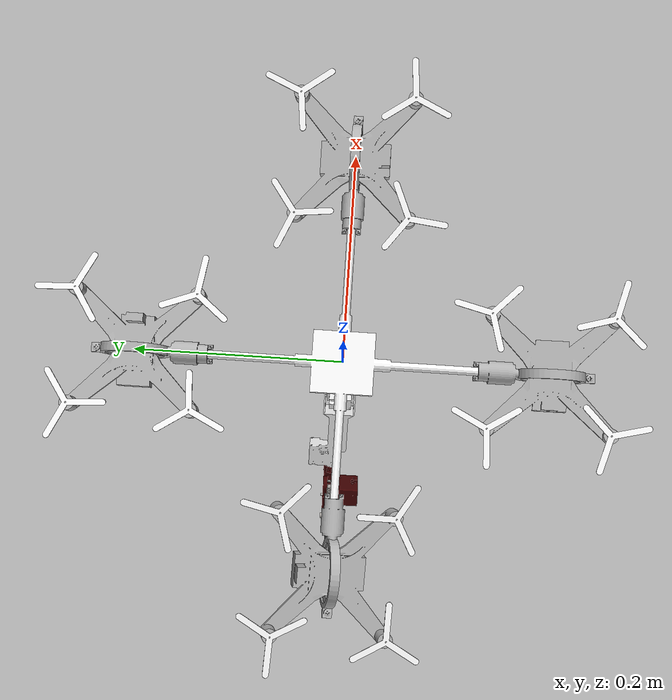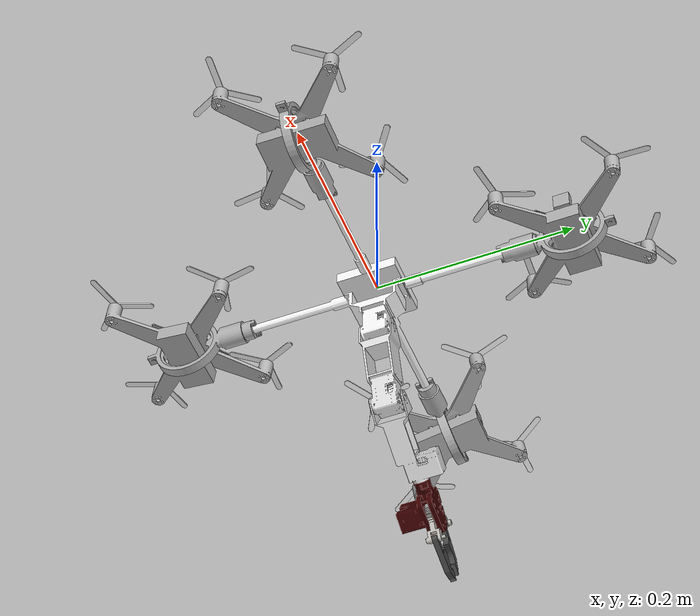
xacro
<?xml version="1.0" encoding="utf-8"?>
<robot
  name="aerialvkc_v3000_description" xmlns:xacro="http://ros.org/wiki/xacro">

  <!-- ==================== COLOR SETTING ====================== -->

  <gazebo reference="base_link">
    <material>Gazebo/DarkGrey</material>
  </gazebo>
  <gazebo reference="hinge_link_I">
    <material>Gazebo/White</material>
  </gazebo>
  <gazebo reference="hinge_link_II">
    <material>Gazebo/White</material>
  </gazebo>
  <gazebo reference="hinge_link_III">
    <material>Gazebo/White</material>
  </gazebo>
  <gazebo reference="hinge_link_IV">
    <material>Gazebo/White</material>
  </gazebo>
  <gazebo reference="crazyflie11/base_link">
    <material>Gazebo/Grey</material>
  </gazebo>
  <gazebo reference="crazyflie22/base_link">
    <material>Gazebo/Grey</material>
  </gazebo>
  <gazebo reference="crazyflie33/base_link">
    <material>Gazebo/Grey</material>
  </gazebo>
  <gazebo reference="crazyflie44/base_link">
    <material>Gazebo/Grey</material>
  </gazebo>
  <gazebo reference="prolink_I_I">
    <material>Gazebo/BlackTransparent</material>
  </gazebo>
  <gazebo reference="prolink_I_II">
    <material>Gazebo/BlackTransparent</material>
  </gazebo>
  <gazebo reference="prolink_I_III">
    <material>Gazebo/BlackTransparent</material>
  </gazebo>
  <gazebo reference="prolink_I_IV">
    <material>Gazebo/BlackTransparent</material>
  </gazebo>
  <gazebo reference="prolink_II_I">
    <material>Gazebo/BlackTransparent</material>
  </gazebo>
  <gazebo reference="prolink_II_II">
    <material>Gazebo/BlackTransparent</material>
  </gazebo>
  <gazebo reference="prolink_II_III">
    <material>Gazebo/BlackTransparent</material>
  </gazebo>
  <gazebo reference="prolink_II_IV">
    <material>Gazebo/BlackTransparent</material>
  </gazebo>
  <gazebo reference="prolink_III_I">
    <material>Gazebo/BlackTransparent</material>
  </gazebo>
  <gazebo reference="prolink_III_II">
    <material>Gazebo/BlackTransparent</material>
  </gazebo>
  <gazebo reference="prolink_III_III">
    <material>Gazebo/BlackTransparent</material>
  </gazebo>
  <gazebo reference="prolink_III_IV">
    <material>Gazebo/BlackTransparent</material>
  </gazebo>
  <gazebo reference="prolink_IV_I">
    <material>Gazebo/BlackTransparent</material>
  </gazebo>
  <gazebo reference="prolink_IV_II">
    <material>Gazebo/BlackTransparent</material>
  </gazebo>
  <gazebo reference="prolink_IV_III">
    <material>Gazebo/BlackTransparent</material>
  </gazebo>
  <gazebo reference="prolink_IV_IV">
    <material>Gazebo/BlackTransparent</material>
  </gazebo>
  <gazebo reference="gripper_base_link">
    <material>Gazebo/DarkGrey</material>
  </gazebo>
  <gazebo reference="arm_link_I">
    <material>Gazebo/White</material>
  </gazebo>
  <gazebo reference="arm_link_II">
    <material>Gazebo/White</material>
  </gazebo>
  <gazebo reference="gear_arm_link_I">
    <material>Gazebo/White</material>
  </gazebo>
  <gazebo reference="gear_arm_link_II">
    <material>Gazebo/White</material>
  </gazebo>
  <gazebo reference="gripper_arm_link_I">
    <material>Gazebo/White</material>
  </gazebo>
  <gazebo reference="gripper_arm_link_II">
    <material>Gazebo/White</material>
  </gazebo>

  <link
    name="base_link">
    <inertial>
      <origin
        xyz="1.48132749672181E-06 -0.000128518507548026 -0.0186756580403975"
        rpy="0 0 0" />
      <mass
        value="0.0852219238436207" />
      <inertia
        ixx="2.92200472097296E-05"
        ixy="-8.40191538166482E-11"
        ixz="1.3785811308194E-09"
        iyy="2.73759047460707E-05"
        iyz="-2.65992896723796E-09"
        izz="5.10775637259083E-05" />
    </inertial>
    <visual>
      <origin
        xyz="0 0 0"
        rpy="0 0 0" />
      <geometry>
        <mesh
          filename="package://aerialvkc_v3000_description/meshes/base_link.STL" />
      </geometry>
      <material
        name="">
        <color
          rgba="1 1 1 1" />
      </material>
    </visual>
    <collision>
      <origin
        xyz="0 0 0"
        rpy="0 0 0" />
      <geometry>
        <mesh
          filename="package://aerialvkc_v3000_description/meshes/base_link.STL" />
      </geometry>
    </collision>
  </link>

<!--================QC1===========================-->
<!--================QC1===========================-->
<!--================QC1===========================-->

  <link
    name="hinge_link_I">
    <inertial>
      <origin
        xyz="-0.0286920658868101 -2.09776640502923E-12 0.000129765701351203"
        rpy="0 0 0" />
      <mass
        value="0.0180481140635355" />
      <inertia
        ixx="1.14996315873899E-06"
        ixy="-2.80155247515752E-16"
        ixz="-4.90018086254004E-14"
        iyy="4.77573925274109E-06"
        iyz="-2.69085765053552E-14"
        izz="4.43859152295461E-06" />
    </inertial>
    <visual>
      <origin
        xyz="0 0 0"
        rpy="0 0 0" />
      <geometry>
        <mesh
          filename="package://aerialvkc_v3000_description/meshes/hinge_link_I.STL" />
      </geometry>
      <material
        name="">
        <color
          rgba="0.698039215686274 0.698039215686274 0.698039215686274 1" />
      </material>
    </visual>
    <collision>
      <origin
        xyz="0 0 0"
        rpy="0 0 0" />
      <geometry>
        <mesh
          filename="package://aerialvkc_v3000_description/meshes/hinge_link_I.STL" />
      </geometry>
    </collision>
  </link>
  <joint
    name="hinge_joint_I"
    type="continuous">
    <origin
      xyz="0 0.200000000000009 -0.00599999999999989"
      rpy="0.00518564126547178 0 1.5707963267949" />
    <parent
      link="base_link" />
    <child
      link="hinge_link_I" />
    <axis
      xyz="1 0 0" />
  </joint>
  <link
    name="crazyflie11/base_link">
    <inertial>
      <origin
        xyz="4.7277807986898E-05 -0.000242548958398092 -0.00256688589947934"
        rpy="0 0 0" />
      <mass
        value="0.0934996333792319" />
      <inertia
        ixx="4.92603412266741E-05"
        ixy="-1.92395335842271E-11"
        ixz="-1.15879177735369E-14"
        iyy="4.17272140348144E-05"
        iyz="2.11721011582016E-07"
        izz="8.39136565814911E-05" />
    </inertial>
    <visual>
      <origin
        xyz="0 0 0"
        rpy="0 0 0" />
      <geometry>
        <mesh
          filename="package://aerialvkc_v3000_description/meshes/crazyflie11/base_link.STL" />
      </geometry>
      <material
        name="">
        <color
          rgba="0.698039215686274 0.698039215686274 0.698039215686274 1" />
      </material>
    </visual>
    <collision>
      <origin
        xyz="0 0 0"
        rpy="0 0 0" />
      <geometry>
        <mesh
          filename="package://aerialvkc_v3000_description/meshes/crazyflie11/base_link.STL" />
      </geometry>
    </collision>
  </link>
  <joint
    name="gimbal_joint_I"
    type="continuous">
    <origin
      xyz="0 0 0"
      rpy="0 -0.00405398778622896 0" />
    <parent
      link="hinge_link_I" />
    <child
      link="crazyflie11/base_link" />
    <axis
      xyz="0 -1 0" />
  </joint>
  <link
    name="prolink_I_I">
    <inertial>
      <origin
        xyz="1.0547118733939E-14 5.20673305899333E-05 0.000500000000002887"
        rpy="0 0 0" />
      <mass
        value="0.000657768846435091" />
      <inertia
        ixx="1.60093905219262E-07"
        ixy="3.04402465419514E-22"
        ixz="1.61145123082987E-22"
        iyy="1.58813263600953E-07"
        iyz="-1.81359349302251E-22"
        izz="3.18797540679143E-07" />
    </inertial>
    <visual>
      <origin
        xyz="0 0 0"
        rpy="0 0 0" />
      <geometry>
        <mesh
          filename="package://aerialvkc_v3000_description/meshes/prolink_I_I.STL" />
      </geometry>
      <material
        name="">
        <color
          rgba="1 1 1 1" />
      </material>
    </visual>
    <collision>
      <origin
        xyz="0 0 0"
        rpy="0 0 0" />
      <geometry>
        <mesh
          filename="package://aerialvkc_v3000_description/meshes/prolink_I_I.STL" />
      </geometry>
    </collision>
  </link>
  <joint
    name="projoint_I_I"
    type="continuous">
    <origin
      xyz="-0.0580370958807339 0.0555608345534356 0.0210499999999688"
      rpy="0 0 1.10424755267301" />
    <parent
      link="crazyflie11/base_link" />
    <child
      link="prolink_I_I" />
    <axis
      xyz="0 0 1" />
  </joint>

  <link
    name="prolink_I_II">
    <inertial>
      <origin
        xyz="-1.04931939338138E-05 5.09990176109087E-05 0.000500000000002998"
        rpy="0 0 0" />
      <mass
        value="0.000657768846435093" />
      <inertia
        ixx="1.60041892161909E-07"
        ixy="2.52793844475622E-10"
        ixz="8.84049279666048E-23"
        iyy="1.58865276658305E-07"
        iyz="-7.82978148569725E-23"
        izz="3.18797540679141E-07" />
    </inertial>
    <visual>
      <origin
        xyz="0 0 0"
        rpy="0 0 0" />
      <geometry>
        <mesh
          filename="package://aerialvkc_v3000_description/meshes/prolink_I_II.STL" />
      </geometry>
      <material
        name="">
        <color
          rgba="1 1 1 1" />
      </material>
    </visual>
    <collision>
      <origin
        xyz="0 0 0"
        rpy="0 0 0" />
      <geometry>
        <mesh
          filename="package://aerialvkc_v3000_description/meshes/prolink_I_II.STL" />
      </geometry>
    </collision>
  </link>
  <joint
    name="projoint_I_II"
    type="continuous">
    <origin
      xyz="0.0580370958812072 0.0555608345539184 0.0210499999999653"
      rpy="0 0 -0.663519439198283" />
    <parent
      link="crazyflie11/base_link" />
    <child
      link="prolink_I_II" />
    <axis
      xyz="0 0 1" />
  </joint>
  <link
    name="prolink_I_III">
    <inertial>
      <origin
        xyz="-1.90407394590197E-06 5.20325034606868E-05 0.000500000000002554"
        rpy="0 0 0" />
      <mass
        value="0.000657768846435069" />
      <inertia
        ixx="1.60092192585075E-07"
        ixy="4.6801041599918E-11"
        ixz="-7.42138109531619E-23"
        iyy="1.58814976235129E-07"
        iyz="-5.5524498617622E-23"
        izz="3.18797540679131E-07" />
    </inertial>
    <visual>
      <origin
        xyz="0 0 0"
        rpy="0 0 0" />
      <geometry>
        <mesh
          filename="package://aerialvkc_v3000_description/meshes/prolink_I_III.STL" />
      </geometry>
      <material
        name="">
        <color
          rgba="1 1 1 1" />
      </material>
    </visual>
    <collision>
      <origin
        xyz="0 0 0"
        rpy="0 0 0" />
      <geometry>
        <mesh
          filename="package://aerialvkc_v3000_description/meshes/prolink_I_III.STL" />
      </geometry>
    </collision>
  </link>
  <joint
    name="projoint_I_III"
    type="continuous">
    <origin
      xyz="0.0580370958804296 -0.0545608345526662 0.0210500000000247"
      rpy="0 0 -1.57077530421496" />
    <parent
      link="crazyflie11/base_link" />
    <child
      link="prolink_I_III" />
    <axis
      xyz="0 0 1" />
  </joint>
  <link
    name="prolink_I_IV">
    <inertial>
      <origin
        xyz="-2.06085148946045E-14 5.20673305122177E-05 0.000500000000002998"
        rpy="0 0 0" />
      <mass
        value="0.000657768846435101" />
      <inertia
        ixx="1.60093905219265E-07"
        ixy="-5.29395592033938E-22"
        ixz="3.44830917858043E-22"
        iyy="1.58813263600954E-07"
        iyz="2.25380867526558E-22"
        izz="3.18797540679146E-07" />
    </inertial>
    <visual>
      <origin
        xyz="0 0 0"
        rpy="0 0 0" />
      <geometry>
        <mesh
          filename="package://aerialvkc_v3000_description/meshes/prolink_I_IV.STL" />
      </geometry>
      <material
        name="">
        <color
          rgba="1 1 1 1" />
      </material>
    </visual>
    <collision>
      <origin
        xyz="0 0 0"
        rpy="0 0 0" />
      <geometry>
        <mesh
          filename="package://aerialvkc_v3000_description/meshes/prolink_I_IV.STL" />
      </geometry>
    </collision>
  </link>
  <joint
    name="projoint_I_IV"
    type="continuous">
    <origin
      xyz="-0.0580370958808196 -0.0545608345536692 0.021050000000026"
      rpy="0 0 2.97788495714067" />
    <parent
      link="crazyflie11/base_link" />
    <child
      link="prolink_I_IV" />
    <axis
      xyz="0 0 1" />
  </joint>

<transmission name="crazy_tilt_1_trans">
    <type>transmission_interface/SimpleTransmission</type>
    <joint name="hinge_joint_I">
      <hardwareInterface>hardware_interface/PositionJointInterface</hardwareInterface>
    </joint>
    <actuator name="hinge_joint_I_motor">
      <hardwareInterface>hardware_interface/PositionJointInterface</hardwareInterface>
      <mechanicalReduction>1</mechanicalReduction>
    </actuator>
  </transmission>
  <transmission name="crazy_twist_1_trans">
      <type>transmission_interface/SimpleTransmission</type>
      <joint name="gimbal_joint_I">
        <hardwareInterface>hardware_interface/PositionJointInterface</hardwareInterface>
      </joint>
      <actuator name="gimbal_joint_I_motor">
        <hardwareInterface>hardware_interface/PositionJointInterface</hardwareInterface>
        <mechanicalReduction>1</mechanicalReduction>
      </actuator>
  </transmission>

  <gazebo>
    <plugin filename="librotors_gazebo_controller_interface.so" name="controller_interface">
      <robotNamespace>crazyflie11</robotNamespace>
      <commandAttitudeThrustSubTopic>command/attitude</commandAttitudeThrustSubTopic>
      <commandRateThrustSubTopic>command/rate</commandRateThrustSubTopic>
      <commandMotorSpeedSubTopic>command/motor_speed</commandMotorSpeedSubTopic>
      <imuSubTopic>imu</imuSubTopic>
      <motorSpeedCommandPubTopic>gazebo/command/motor_speed</motorSpeedCommandPubTopic>
    </plugin>
  </gazebo>
  <gazebo>
    <plugin filename="librotors_gazebo_mavlink_interface.so" name="mavlink_interface">
      <robotNamespace>crazyflie11</robotNamespace>
      <mavlinkControlSubTopic>/mavlink/from</mavlinkControlSubTopic>
      <imuSubTopic>imu</imuSubTopic>
      <mavlinkHilSensorPubTopic>/mavlink/to</mavlinkHilSensorPubTopic>
      <motorSpeedsPubTopic>gazebo/command/motor_speed</motorSpeedsPubTopic>
      <gpsUpdateFreq>5.0</gpsUpdateFreq>
      <!-- Frequency of HIL GPS messages [Hz] -->
      <rotorCount>4</rotorCount>
      <referenceMagNorth>0.21475</referenceMagNorth>
      <referenceMagEast>0.00797</referenceMagEast>
      <referenceMagDown>0.42817</referenceMagDown>
      <referenceLatitude>47.3667</referenceLatitude>
      <!-- the initial latitude [degrees [-90, 90]] -->
      <referenceLongitude>8.55</referenceLongitude>
      <!-- the initial longitude [degrees [-180, 180]] -->
      <referenceAltitude>500.0</referenceAltitude>
      <!-- the initial altitude [m] -->
    </plugin>
  </gazebo>
  <gazebo>
    <plugin filename="librotors_gazebo_multirotor_base_plugin.so" name="multirotor_base_plugin">
      <robotNamespace>crazyflie11</robotNamespace>
      <linkName>crazyflie11/base_link</linkName>
      <rotorVelocitySlowdownSim>50</rotorVelocitySlowdownSim>
    </plugin>
  </gazebo>
   <gazebo>
    <plugin filename="librotors_gazebo_motor_model.so" name="crazyflie11_front-right_motor_model">
      <robotNamespace>crazyflie11</robotNamespace>
      <jointName>projoint_I_III</jointName>
      <linkName>prolink_I_III</linkName>
      <turningDirection>ccw</turningDirection>
      <timeConstantUp>0.0125</timeConstantUp>
      <timeConstantDown>0.025</timeConstantDown>
      <maxRotVelocity>4000</maxRotVelocity>
      <motorConstant>1.28192e-08</motorConstant>
      <momentConstant>0.005964552</momentConstant>
      <commandSubTopic>gazebo/command/motor_speed</commandSubTopic>
      <motorNumber>0</motorNumber>
      <rotorDragCoefficient>8.06428e-05</rotorDragCoefficient>
      <rollingMomentCoefficient>1e-06</rollingMomentCoefficient>
      <motorSpeedPubTopic>motor_speed/0</motorSpeedPubTopic>
      <rotorVelocitySlowdownSim>50</rotorVelocitySlowdownSim>
    </plugin>
  </gazebo>
  <gazebo>
    <plugin filename="librotors_gazebo_motor_model.so" name="crazyflie11_back-right_motor_model">
      <robotNamespace>crazyflie11</robotNamespace>
      <jointName>projoint_I_IV</jointName>
      <linkName>prolink_I_IV</linkName>
      <turningDirection>cw</turningDirection>
      <timeConstantUp>0.0125</timeConstantUp>
      <timeConstantDown>0.025</timeConstantDown>
      <maxRotVelocity>4000</maxRotVelocity>
      <motorConstant>1.28192e-08</motorConstant>
      <momentConstant>0.005964552</momentConstant>
      <commandSubTopic>gazebo/command/motor_speed</commandSubTopic>
      <motorNumber>1</motorNumber>
      <rotorDragCoefficient>8.06428e-05</rotorDragCoefficient>
      <rollingMomentCoefficient>1e-06</rollingMomentCoefficient>
      <motorSpeedPubTopic>motor_speed/1</motorSpeedPubTopic>
      <rotorVelocitySlowdownSim>50</rotorVelocitySlowdownSim>
    </plugin>
  </gazebo>
  <gazebo>
    <plugin filename="librotors_gazebo_motor_model.so" name="crazyflie11_back-left_motor_model">
      <robotNamespace>crazyflie11</robotNamespace>
      <jointName>projoint_I_I</jointName>
      <linkName>prolink_I_I</linkName>
      <turningDirection>ccw</turningDirection>
      <timeConstantUp>0.0125</timeConstantUp>
      <timeConstantDown>0.025</timeConstantDown>
      <maxRotVelocity>4000</maxRotVelocity>
      <motorConstant>1.28192e-08</motorConstant>
      <momentConstant>0.005964552</momentConstant>
      <commandSubTopic>gazebo/command/motor_speed</commandSubTopic>
      <motorNumber>2</motorNumber>
      <rotorDragCoefficient>8.06428e-05</rotorDragCoefficient>
      <rollingMomentCoefficient>1e-06</rollingMomentCoefficient>
      <motorSpeedPubTopic>motor_speed/2</motorSpeedPubTopic>
      <rotorVelocitySlowdownSim>50</rotorVelocitySlowdownSim>
    </plugin>
  </gazebo>
  <gazebo>
    <plugin filename="librotors_gazebo_motor_model.so" name="crazyflie11_front-left_motor_model">
      <robotNamespace>crazyflie11</robotNamespace>
      <jointName>projoint_I_II</jointName>
      <linkName>prolink_I_II</linkName>
      <turningDirection>cw</turningDirection>
      <timeConstantUp>0.0125</timeConstantUp>
      <timeConstantDown>0.025</timeConstantDown>
      <maxRotVelocity>4000</maxRotVelocity>
      <motorConstant>1.28192e-08</motorConstant>
      <momentConstant>0.005964552</momentConstant>
      <commandSubTopic>gazebo/command/motor_speed</commandSubTopic>
      <motorNumber>3</motorNumber>
      <rotorDragCoefficient>8.06428e-05</rotorDragCoefficient>
      <rollingMomentCoefficient>1e-06</rollingMomentCoefficient>
      <motorSpeedPubTopic>motor_speed/3</motorSpeedPubTopic>
      <rotorVelocitySlowdownSim>50</rotorVelocitySlowdownSim>
    </plugin>
  </gazebo>

  <!-- ==================== ROS INTERFACE MACRO ====================== -->
   <xacro:macro
      name="ros_interface_plugin_macro"
      params="namespace">
    <gazebo>
      <plugin name="ros_interface_plugin" filename="librotors_gazebo_ros_interface_plugin.so">
        <robotNamespace>${namespace}</robotNamespace>
      </plugin>
    </gazebo>
  </xacro:macro>

<!--================QC2===========================-->
<!--================QC2===========================-->
<!--================QC2===========================-->

  <link
    name="hinge_link_II">
    <inertial>
      <origin
        xyz="-0.0286920658625174 -6.13620265710324E-13 0.000129766128506792"
        rpy="0 0 0" />
      <mass
        value="0.0180481140584542" />
      <inertia
        ixx="1.1499631662955E-06"
        ixy="5.61120378748299E-20"
        ixz="2.47952921767015E-18"
        iyy="4.77573926634576E-06"
        iyz="-2.39120533973003E-14"
        izz="4.43859151899919E-06" />
    </inertial>
    <visual>
      <origin
        xyz="0 0 0"
        rpy="0 0 0" />
      <geometry>
        <mesh
          filename="package://aerialvkc_v3000_description/meshes/hinge_link_II.STL" />
      </geometry>
      <material
        name="">
        <color
          rgba="0.698039215686274 0.698039215686274 0.698039215686274 1" />
      </material>
    </visual>
    <collision>
      <origin
        xyz="0 0 0"
        rpy="0 0 0" />
      <geometry>
        <mesh
          filename="package://aerialvkc_v3000_description/meshes/hinge_link_II.STL" />
      </geometry>
    </collision>
  </link>
  <joint
    name="hinge_joint_II"
    type="continuous">
    <origin
      xyz="0.199999999999998 0 -0.00600000000000039"
      rpy="-0.0287956813296177 0 0" />
    <parent
      link="base_link" />
    <child
      link="hinge_link_II" />
    <axis
      xyz="1 0 0" />
  </joint>
  <link
    name="crazyflie22/base_link">
    <inertial>
      <origin
        xyz="0.000260025205274461 -0.000242548958405142 -0.00255411928161065"
        rpy="0 0 0" />
      <mass
        value="0.0934996333792317" />
      <inertia
        ixx="4.94987515477189E-05"
        ixy="-1.75803692106723E-08"
        ixz="-2.86441417358484E-06"
        iyy="4.17272140348139E-05"
        iyz="2.10989852183832E-07"
        izz="8.36752462604459E-05" />
    </inertial>
    <visual>
      <origin
        xyz="0 0 0"
        rpy="0 0 0" />
      <geometry>
        <mesh
          filename="package://aerialvkc_v3000_description/meshes/crazyflie22/base_link.STL" />
      </geometry>
      <material
        name="">
        <color
          rgba="0.698039215686274 0.698039215686274 0.698039215686274 1" />
      </material>
    </visual>
    <collision>
      <origin
        xyz="0 0 0"
        rpy="0 0 0" />
      <geometry>
        <mesh
          filename="package://aerialvkc_v3000_description/meshes/crazyflie22/base_link.STL" />
      </geometry>
    </collision>
  </link>
  <joint
    name="gimbal_joint_II"
    type="continuous">
    <origin
      xyz="0 0 0"
      rpy="0 0 0" />
    <parent
      link="hinge_link_II" />
    <child
      link="crazyflie22/base_link" />
    <axis
      xyz="0 -1 0" />
  </joint>
  <link
    name="prolink_II_I">
    <inertial>
      <origin
        xyz="7.51482209793153E-13 -5.20673301678265E-05 0.00049999999979089"
        rpy="0 0 0" />
      <mass
        value="0.000657768846435077" />
      <inertia
        ixx="1.60093905219261E-07"
        ixy="1.9124415762226E-21"
        ixz="1.34416849539867E-22"
        iyy="1.58813263600949E-07"
        iyz="-3.53619711866419E-22"
        izz="3.18797540679137E-07" />
    </inertial>
    <visual>
      <origin
        xyz="0 0 0"
        rpy="0 0 0" />
      <geometry>
        <mesh
          filename="package://aerialvkc_v3000_description/meshes/prolink_II_I.STL" />
      </geometry>
      <material
        name="">
        <color
          rgba="1 1 1 1" />
      </material>
    </visual>
    <collision>
      <origin
        xyz="0 0 0"
        rpy="0 0 0" />
      <geometry>
        <mesh
          filename="package://aerialvkc_v3000_description/meshes/prolink_II_I.STL" />
      </geometry>
    </collision>
  </link>
  <joint
    name="projoint_II_I"
    type="continuous">
    <origin
      xyz="-0.0595830993828221 0.0555608345545135 0.0161635783847631"
      rpy="0.0755920970039211 0.0344063484778542 -1.99713839703144" />
    <parent
      link="crazyflie22/base_link" />
    <child
      link="prolink_II_I" />
    <axis
      xyz="0 0 1" />
  </joint>
  <link
    name="prolink_II_II">
    <inertial>
      <origin
        xyz="-5.18683221605309E-05 4.54797229854087E-06 0.000499999999773015"
        rpy="0 0 0" />
      <mass
        value="0.000657768846435096" />
      <inertia
        ixx="1.58823034455358E-07"
        ixy="1.1143380637116E-10"
        ixz="7.4032664823496E-23"
        iyy="1.60084134364856E-07"
        iyz="-6.82940993239093E-22"
        izz="3.18797540679142E-07" />
    </inertial>
    <visual>
      <origin
        xyz="0 0 0"
        rpy="0 0 0" />
      <geometry>
        <mesh
          filename="package://aerialvkc_v3000_description/meshes/prolink_II_II.STL" />
      </geometry>
      <material
        name="">
        <color
          rgba="1 1 1 1" />
      </material>
    </visual>
    <collision>
      <origin
        xyz="0 0 0"
        rpy="0 0 0" />
      <geometry>
        <mesh
          filename="package://aerialvkc_v3000_description/meshes/prolink_II_II.STL" />
      </geometry>
    </collision>
  </link>
  <joint
    name="projoint_II_II"
    type="continuous">
    <origin
      xyz="0.0560911155447258 0.055560834553689 0.0257913503949391"
      rpy="0.0784644863410207 0.0272130660534785 -1.90396164537388" />
    <parent
      link="crazyflie22/base_link" />
    <child
      link="prolink_II_II" />
    <axis
      xyz="0 0 1" />
  </joint>
  <link
    name="prolink_II_III">
    <inertial>
      <origin
        xyz="-2.07419986428536E-05 4.77574748815046E-05 0.000499999999740819"
        rpy="0 0 0" />
      <mass
        value="0.000657768846435079" />
      <inertia
        ixx="1.59890670359717E-07"
        ixy="4.67938683258318E-10"
        ixz="-1.84047686293049E-22"
        iyy="1.59016498460492E-07"
        iyz="3.83811804224605E-22"
        izz="3.18797540679136E-07" />
    </inertial>
    <visual>
      <origin
        xyz="0 0 0"
        rpy="0 0 0" />
      <geometry>
        <mesh
          filename="package://aerialvkc_v3000_description/meshes/prolink_II_III.STL" />
      </geometry>
      <material
        name="">
        <color
          rgba="1 1 1 1" />
      </material>
    </visual>
    <collision>
      <origin
        xyz="0 0 0"
        rpy="0 0 0" />
      <geometry>
        <mesh
          filename="package://aerialvkc_v3000_description/meshes/prolink_II_III.STL" />
      </geometry>
    </collision>
  </link>
  <joint
    name="projoint_II_III"
    type="continuous">
    <origin
      xyz="0.0560911155449499 -0.0545608345531821 0.0257913503949986"
      rpy="0.0784644863410329 0.0272130660534786 -1.90396164537387" />
    <parent
      link="crazyflie22/base_link" />
    <child
      link="prolink_II_III" />
    <axis
      xyz="0 0 1" />
  </joint>
  <link
    name="prolink_II_IV">
    <inertial>
      <origin
        xyz="5.09296222228339E-05 1.08249937225136E-05 0.000499999999742429"
        rpy="0 0 0" />
      <mass
        value="0.000657768846435079" />
      <inertia
        ixx="1.58868618017891E-07"
        ixy="-2.6043244539803E-10"
        ixz="-2.72969602142499E-23"
        iyy="1.60038550802321E-07"
        iyz="-3.76884166594473E-22"
        izz="3.18797540679139E-07" />
    </inertial>
    <visual>
      <origin
        xyz="0 0 0"
        rpy="0 0 0" />
      <geometry>
        <mesh
          filename="package://aerialvkc_v3000_description/meshes/prolink_II_IV.STL" />
      </geometry>
      <material
        name="">
        <color
          rgba="1 1 1 1" />
      </material>
    </visual>
    <collision>
      <origin
        xyz="0 0 0"
        rpy="0 0 0" />
      <geometry>
        <mesh
          filename="package://aerialvkc_v3000_description/meshes/prolink_II_IV.STL" />
      </geometry>
    </collision>
  </link>
  <joint
    name="projoint_II_IV"
    type="continuous">
    <origin
      xyz="-0.0595830993831619 -0.0545608345535355 0.0161635783847945"
      rpy="0.0784644863410271 0.0272130660534784 -1.90396164537389" />
    <parent
      link="crazyflie22/base_link" />
    <child
      link="prolink_II_IV" />
    <axis
      xyz="0 0 1" />
  </joint>

  <transmission name="crazy_tilt_2_trans">
    <type>transmission_interface/SimpleTransmission</type>
    <joint name="hinge_joint_II">
      <hardwareInterface>hardware_interface/PositionJointInterface</hardwareInterface>
    </joint>
    <actuator name="hinge_joint_II_motor">
      <hardwareInterface>hardware_interface/PositionJointInterface</hardwareInterface>
      <mechanicalReduction>1</mechanicalReduction>
    </actuator>
  </transmission>
  <transmission name="crazy_twist_2_trans">
      <type>transmission_interface/SimpleTransmission</type>
      <joint name="gimbal_joint_II">
        <hardwareInterface>hardware_interface/PositionJointInterface</hardwareInterface>
      </joint>
      <actuator name="gimbal_joint_II_motor">
        <hardwareInterface>hardware_interface/PositionJointInterface</hardwareInterface>
        <mechanicalReduction>1</mechanicalReduction>
      </actuator>
  </transmission>

  <gazebo>
    <plugin filename="librotors_gazebo_controller_interface.so" name="controller_interface">
      <robotNamespace>crazyflie22</robotNamespace>
      <commandAttitudeThrustSubTopic>command/attitude</commandAttitudeThrustSubTopic>
      <commandRateThrustSubTopic>command/rate</commandRateThrustSubTopic>
      <commandMotorSpeedSubTopic>command/motor_speed</commandMotorSpeedSubTopic>
      <imuSubTopic>imu</imuSubTopic>
      <motorSpeedCommandPubTopic>gazebo/command/motor_speed</motorSpeedCommandPubTopic>
    </plugin>
  </gazebo>
  <gazebo>
    <plugin filename="librotors_gazebo_mavlink_interface.so" name="mavlink_interface">
      <robotNamespace>crazyflie22</robotNamespace>
      <mavlinkControlSubTopic>/mavlink/from</mavlinkControlSubTopic>
      <imuSubTopic>imu</imuSubTopic>
      <mavlinkHilSensorPubTopic>/mavlink/to</mavlinkHilSensorPubTopic>
      <motorSpeedsPubTopic>gazebo/command/motor_speed</motorSpeedsPubTopic>
      <gpsUpdateFreq>5.0</gpsUpdateFreq>
      <!-- Frequency of HIL GPS messages [Hz] -->
      <rotorCount>4</rotorCount>
      <referenceMagNorth>0.21475</referenceMagNorth>
      <referenceMagEast>0.00797</referenceMagEast>
      <referenceMagDown>0.42817</referenceMagDown>
      <referenceLatitude>47.3667</referenceLatitude>
      <!-- the initial latitude [degrees [-90, 90]] -->
      <referenceLongitude>8.55</referenceLongitude>
      <!-- the initial longitude [degrees [-180, 180]] -->
      <referenceAltitude>500.0</referenceAltitude>
      <!-- the initial altitude [m] -->
    </plugin>
  </gazebo>
  <gazebo>
    <plugin filename="librotors_gazebo_multirotor_base_plugin.so" name="multirotor_base_plugin">
      <robotNamespace>crazyflie22</robotNamespace>
      <linkName>crazyflie22/base_link</linkName>
      <rotorVelocitySlowdownSim>50</rotorVelocitySlowdownSim>
    </plugin>
  </gazebo>
   <gazebo>
    <plugin filename="librotors_gazebo_motor_model.so" name="crazyflie22_front-right_motor_model">
      <robotNamespace>crazyflie22</robotNamespace>
      <jointName>projoint_II_III</jointName>
      <linkName>prolink_II_III</linkName>
      <turningDirection>ccw</turningDirection>
      <timeConstantUp>0.0125</timeConstantUp>
      <timeConstantDown>0.025</timeConstantDown>
      <maxRotVelocity>4000</maxRotVelocity>
      <motorConstant>1.28192e-08</motorConstant>
      <momentConstant>0.005964552</momentConstant>
      <commandSubTopic>gazebo/command/motor_speed</commandSubTopic>
      <motorNumber>0</motorNumber>
      <rotorDragCoefficient>8.06428e-05</rotorDragCoefficient>
      <rollingMomentCoefficient>1e-06</rollingMomentCoefficient>
      <motorSpeedPubTopic>motor_speed/0</motorSpeedPubTopic>
      <rotorVelocitySlowdownSim>50</rotorVelocitySlowdownSim>
    </plugin>
  </gazebo>
  <gazebo>
    <plugin filename="librotors_gazebo_motor_model.so" name="crazyflie22_back-right_motor_model">
      <robotNamespace>crazyflie22</robotNamespace>
      <jointName>projoint_II_IV</jointName>
      <linkName>prolink_II_IV</linkName>
      <turningDirection>cw</turningDirection>
      <timeConstantUp>0.0125</timeConstantUp>
      <timeConstantDown>0.025</timeConstantDown>
      <maxRotVelocity>4000</maxRotVelocity>
      <motorConstant>1.28192e-08</motorConstant>
      <momentConstant>0.005964552</momentConstant>
      <commandSubTopic>gazebo/command/motor_speed</commandSubTopic>
      <motorNumber>1</motorNumber>
      <rotorDragCoefficient>8.06428e-05</rotorDragCoefficient>
      <rollingMomentCoefficient>1e-06</rollingMomentCoefficient>
      <motorSpeedPubTopic>motor_speed/1</motorSpeedPubTopic>
      <rotorVelocitySlowdownSim>50</rotorVelocitySlowdownSim>
    </plugin>
  </gazebo>
  <gazebo>
    <plugin filename="librotors_gazebo_motor_model.so" name="crazyflie22_back-left_motor_model">
      <robotNamespace>crazyflie22</robotNamespace>
      <jointName>projoint_II_I</jointName>
      <linkName>prolink_II_I</linkName>
      <turningDirection>ccw</turningDirection>
      <timeConstantUp>0.0125</timeConstantUp>
      <timeConstantDown>0.025</timeConstantDown>
      <maxRotVelocity>4000</maxRotVelocity>
      <motorConstant>1.28192e-08</motorConstant>
      <momentConstant>0.005964552</momentConstant>
      <commandSubTopic>gazebo/command/motor_speed</commandSubTopic>
      <motorNumber>2</motorNumber>
      <rotorDragCoefficient>8.06428e-05</rotorDragCoefficient>
      <rollingMomentCoefficient>1e-06</rollingMomentCoefficient>
      <motorSpeedPubTopic>motor_speed/2</motorSpeedPubTopic>
      <rotorVelocitySlowdownSim>50</rotorVelocitySlowdownSim>
    </plugin>
  </gazebo>
  <gazebo>
    <plugin filename="librotors_gazebo_motor_model.so" name="crazyflie22_front-left_motor_model">
      <robotNamespace>crazyflie22</robotNamespace>
      <jointName>projoint_II_II</jointName>
      <linkName>prolink_II_II</linkName>
      <turningDirection>cw</turningDirection>
      <timeConstantUp>0.0125</timeConstantUp>
      <timeConstantDown>0.025</timeConstantDown>
      <maxRotVelocity>4000</maxRotVelocity>
      <motorConstant>1.28192e-08</motorConstant>
      <momentConstant>0.005964552</momentConstant>
      <commandSubTopic>gazebo/command/motor_speed</commandSubTopic>
      <motorNumber>3</motorNumber>
      <rotorDragCoefficient>8.06428e-05</rotorDragCoefficient>
      <rollingMomentCoefficient>1e-06</rollingMomentCoefficient>
      <motorSpeedPubTopic>motor_speed/3</motorSpeedPubTopic>
      <rotorVelocitySlowdownSim>50</rotorVelocitySlowdownSim>
    </plugin>
  </gazebo>

  <!-- ==================== ROS INTERFACE MACRO ====================== -->

<!--================QC3===========================-->
<!--================QC3===========================-->
<!--================QC3===========================-->

  <link
    name="hinge_link_III">
    <inertial>
      <origin
        xyz="-0.0286920658808958 2.18658424699925E-13 0.000129766128801556"
        rpy="0 0 0" />
      <mass
        value="0.0180481140621349" />
      <inertia
        ixx="1.14996316009685E-06"
        ixy="7.66630253772555E-21"
        ixz="-8.6233529577341E-19"
        iyy="4.77573925518498E-06"
        iyz="-2.63595495794425E-14"
        izz="4.43859152224334E-06" />
    </inertial>
    <visual>
      <origin
        xyz="0 0 0"
        rpy="0 0 0" />
      <geometry>
        <mesh
          filename="package://aerialvkc_v3000_description/meshes/hinge_link_III.STL" />
      </geometry>
      <material
        name="">
        <color
          rgba="0.698039215686274 0.698039215686274 0.698039215686274 1" />
      </material>
    </visual>
    <collision>
      <origin
        xyz="0 0 0"
        rpy="0 0 0" />
      <geometry>
        <mesh
          filename="package://aerialvkc_v3000_description/meshes/hinge_link_III.STL" />
      </geometry>
    </collision>
  </link>
  <joint
    name="hinge_joint_III"
    type="continuous">
    <origin
      xyz="0 -0.2 -0.00600000000000006"
      rpy="0.010335172419835 0 -1.5707963267949" />
    <parent
      link="base_link" />
    <child
      link="hinge_link_III" />
    <axis
      xyz="1 0 0" />
  </joint>
  <link
    name="crazyflie33/base_link">
    <inertial>
      <origin
        xyz="4.72778079948499E-05 -0.000242548958406419 -0.00256688589947895"
        rpy="0 0 0" />
      <mass
        value="0.0934996333792321" />
      <inertia
        ixx="4.92603412266742E-05"
        ixy="-1.92395334444135E-11"
        ixz="-1.15879799245794E-14"
        iyy="4.17272140348142E-05"
        iyz="2.11721011560071E-07"
        izz="8.39136565814913E-05" />
    </inertial>
    <visual>
      <origin
        xyz="0 0 0"
        rpy="0 0 0" />
      <geometry>
        <mesh
          filename="package://aerialvkc_v3000_description/meshes/crazyflie33/base_link.STL" />
      </geometry>
      <material
        name="">
        <color
          rgba="0.698039215686274 0.698039215686274 0.698039215686274 1" />
      </material>
    </visual>
    <collision>
      <origin
        xyz="0 0 0"
        rpy="0 0 0" />
      <geometry>
        <mesh
          filename="package://aerialvkc_v3000_description/meshes/crazyflie33/base_link.STL" />
      </geometry>
    </collision>
  </link>
  <joint
    name="gimbal_joint_III"
    type="continuous">
    <origin
      xyz="0 0 0"
      rpy="0 -0.127462557808115 0" />
    <parent
      link="hinge_link_III" />
    <child
      link="crazyflie33/base_link" />
    <axis
      xyz="0 -1 0" />
  </joint>
  <link
    name="prolink_III_I">
    <inertial>
      <origin
        xyz="-1.7216775078599E-05 -4.9138471421073E-05 0.000499999999804657"
        rpy="0 0 0" />
      <mass
        value="0.000657768846435086" />
      <inertia
        ixx="1.59953881825124E-07"
        ixy="-3.99641383195494E-10"
        ixz="-3.58892988271445E-22"
        iyy="1.58953286995089E-07"
        iyz="2.06795153138257E-22"
        izz="3.18797540679141E-07" />
    </inertial>
    <visual>
      <origin
        xyz="0 0 0"
        rpy="0 0 0" />
      <geometry>
        <mesh
          filename="package://aerialvkc_v3000_description/meshes/prolink_III_I.STL" />
      </geometry>
      <material
        name="">
        <color
          rgba="1 1 1 1" />
      </material>
    </visual>
    <collision>
      <origin
        xyz="0 0 0"
        rpy="0 0 0" />
      <geometry>
        <mesh
          filename="package://aerialvkc_v3000_description/meshes/prolink_III_I.STL" />
      </geometry>
    </collision>
  </link>
  <joint
    name="projoint_III_I"
    type="continuous">
    <origin
      xyz="-0.0580370958826119 0.0555608345531589 0.0210500000001814"
      rpy="0 0 -1.48966793031658" />
    <parent
      link="crazyflie33/base_link" />
    <child
      link="prolink_III_I" />
    <axis
      xyz="0 0 1" />
  </joint>
  <link
    name="prolink_III_II">
    <inertial>
      <origin
        xyz="-4.92400494522816E-05 1.69240829440698E-05 0.000500000000147938"
        rpy="0 0 0" />
      <mass
        value="0.000657768846435089" />
      <inertia
        ixx="1.58948566542123E-07"
        ixy="3.93659359918973E-10"
        ixz="-1.14978105144871E-22"
        iyy="1.59958602278093E-07"
        iyz="-4.96308367531817E-23"
        izz="3.18797540679144E-07" />
    </inertial>
    <visual>
      <origin
        xyz="0 0 0"
        rpy="0 0 0" />
      <geometry>
        <mesh
          filename="package://aerialvkc_v3000_description/meshes/prolink_III_II.STL" />
      </geometry>
      <material
        name="">
        <color
          rgba="1 1 1 1" />
      </material>
    </visual>
    <collision>
      <origin
        xyz="0 0 0"
        rpy="0 0 0" />
      <geometry>
        <mesh
          filename="package://aerialvkc_v3000_description/meshes/prolink_III_II.STL" />
      </geometry>
    </collision>
  </link>
  <joint
    name="projoint_III_II"
    type="continuous">
    <origin
      xyz="0.0580370958807384 0.0555608345530176 0.0210499999999164"
      rpy="0 0 -1.48966793031658" />
    <parent
      link="crazyflie33/base_link" />
    <child
      link="prolink_III_II" />
    <axis
      xyz="0 0 1" />
  </joint>
  <link
    name="prolink_III_III">
    <inertial>
      <origin
        xyz="-8.61076095515223E-06 5.13503811269134E-05 0.000499999999975576"
        rpy="0 0 0" />
      <mass
        value="0.000657768846435087" />
      <inertia
        ixx="1.60058880069487E-07"
        ixy="2.08872935955854E-10"
        ixz="-1.69778820726509E-22"
        iyy="1.58848288750731E-07"
        iyz="-2.81241408268029E-22"
        izz="3.18797540679146E-07" />
    </inertial>
    <visual>
      <origin
        xyz="0 0 0"
        rpy="0 0 0" />
      <geometry>
        <mesh
          filename="package://aerialvkc_v3000_description/meshes/prolink_III_III.STL" />
      </geometry>
      <material
        name="">
        <color
          rgba="1 1 1 1" />
      </material>
    </visual>
    <collision>
      <origin
        xyz="0 0 0"
        rpy="0 0 0" />
      <geometry>
        <mesh
          filename="package://aerialvkc_v3000_description/meshes/prolink_III_III.STL" />
      </geometry>
    </collision>
  </link>
  <joint
    name="projoint_III_III"
    type="continuous">
    <origin
      xyz="0.0580370958809432 -0.0545608345538356 0.0210500000000353"
      rpy="0 0 -1.4896679303166" />
    <parent
      link="crazyflie33/base_link" />
    <child
      link="prolink_III_III" />
    <axis
      xyz="0 0 1" />
  </joint>
  <link
    name="prolink_III_IV">
    <inertial>
      <origin
        xyz="5.20369407975285E-05 -1.77857149941119E-06 0.000500000000126288"
        rpy="0 0 0" />
      <mass
        value="0.000657768846435082" />
      <inertia
        ixx="1.58814757901547E-07"
        ixy="4.37199107530133E-11"
        ixz="1.05465528100511E-22"
        iyy="1.60092410918667E-07"
        iyz="-5.62482816536059E-23"
        izz="3.18797540679141E-07" />
    </inertial>
    <visual>
      <origin
        xyz="0 0 0"
        rpy="0 0 0" />
      <geometry>
        <mesh
          filename="package://aerialvkc_v3000_description/meshes/prolink_III_IV.STL" />
      </geometry>
      <material
        name="">
        <color
          rgba="1 1 1 1" />
      </material>
    </visual>
    <collision>
      <origin
        xyz="0 0 0"
        rpy="0 0 0" />
      <geometry>
        <mesh
          filename="package://aerialvkc_v3000_description/meshes/prolink_III_IV.STL" />
      </geometry>
    </collision>
  </link>
  <joint
    name="projoint_III_IV"
    type="continuous">
    <origin
      xyz="-0.0580370958772718 -0.0545608345588964 0.0210499999999432"
      rpy="0 0 -1.4896679303166" />
    <parent
      link="crazyflie33/base_link" />
    <child
      link="prolink_III_IV" />
    <axis
      xyz="0 0 1" />
  </joint>

  <transmission name="crazy_tilt_3_trans">
    <type>transmission_interface/SimpleTransmission</type>
    <joint name="hinge_joint_III">
      <hardwareInterface>hardware_interface/PositionJointInterface</hardwareInterface>
    </joint>
    <actuator name="hinge_joint_III_motor">
      <hardwareInterface>hardware_interface/PositionJointInterface</hardwareInterface>
      <mechanicalReduction>1</mechanicalReduction>
    </actuator>
  </transmission>
  <transmission name="crazy_twist_3_trans">
      <type>transmission_interface/SimpleTransmission</type>
      <joint name="gimbal_joint_III">
        <hardwareInterface>hardware_interface/PositionJointInterface</hardwareInterface>
      </joint>
      <actuator name="gimbal_joint_III_motor">
        <hardwareInterface>hardware_interface/PositionJointInterface</hardwareInterface>
        <mechanicalReduction>1</mechanicalReduction>
      </actuator>
  </transmission>

  <gazebo>
    <plugin filename="librotors_gazebo_controller_interface.so" name="controller_interface">
      <robotNamespace>crazyflie33</robotNamespace>
      <commandAttitudeThrustSubTopic>command/attitude</commandAttitudeThrustSubTopic>
      <commandRateThrustSubTopic>command/rate</commandRateThrustSubTopic>
      <commandMotorSpeedSubTopic>command/motor_speed</commandMotorSpeedSubTopic>
      <imuSubTopic>imu</imuSubTopic>
      <motorSpeedCommandPubTopic>gazebo/command/motor_speed</motorSpeedCommandPubTopic>
    </plugin>
  </gazebo>
  <gazebo>
    <plugin filename="librotors_gazebo_mavlink_interface.so" name="mavlink_interface">
      <robotNamespace>crazyflie33</robotNamespace>
      <mavlinkControlSubTopic>/mavlink/from</mavlinkControlSubTopic>
      <imuSubTopic>imu</imuSubTopic>
      <mavlinkHilSensorPubTopic>/mavlink/to</mavlinkHilSensorPubTopic>
      <motorSpeedsPubTopic>gazebo/command/motor_speed</motorSpeedsPubTopic>
      <gpsUpdateFreq>5.0</gpsUpdateFreq>
      <!-- Frequency of HIL GPS messages [Hz] -->
      <rotorCount>4</rotorCount>
      <referenceMagNorth>0.21475</referenceMagNorth>
      <referenceMagEast>0.00797</referenceMagEast>
      <referenceMagDown>0.42817</referenceMagDown>
      <referenceLatitude>47.3667</referenceLatitude>
      <!-- the initial latitude [degrees [-90, 90]] -->
      <referenceLongitude>8.55</referenceLongitude>
      <!-- the initial longitude [degrees [-180, 180]] -->
      <referenceAltitude>500.0</referenceAltitude>
      <!-- the initial altitude [m] -->
    </plugin>
  </gazebo>
  <gazebo>
    <plugin filename="librotors_gazebo_multirotor_base_plugin.so" name="multirotor_base_plugin">
      <robotNamespace>crazyflie33</robotNamespace>
      <linkName>crazyflie33/base_link</linkName>
      <rotorVelocitySlowdownSim>50</rotorVelocitySlowdownSim>
    </plugin>
  </gazebo>
   <gazebo>
    <plugin filename="librotors_gazebo_motor_model.so" name="crazyflie33_front-right_motor_model">
      <robotNamespace>crazyflie33</robotNamespace>
      <jointName>projoint_III_III</jointName>
      <linkName>prolink_III_III</linkName>
      <turningDirection>ccw</turningDirection>
      <timeConstantUp>0.0125</timeConstantUp>
      <timeConstantDown>0.025</timeConstantDown>
      <maxRotVelocity>4000</maxRotVelocity>
      <motorConstant>1.28192e-08</motorConstant>
      <momentConstant>0.005964552</momentConstant>
      <commandSubTopic>gazebo/command/motor_speed</commandSubTopic>
      <motorNumber>0</motorNumber>
      <rotorDragCoefficient>8.06428e-05</rotorDragCoefficient>
      <rollingMomentCoefficient>1e-06</rollingMomentCoefficient>
      <motorSpeedPubTopic>motor_speed/0</motorSpeedPubTopic>
      <rotorVelocitySlowdownSim>50</rotorVelocitySlowdownSim>
    </plugin>
  </gazebo>
  <gazebo>
    <plugin filename="librotors_gazebo_motor_model.so" name="crazyflie33_back-right_motor_model">
      <robotNamespace>crazyflie33</robotNamespace>
      <jointName>projoint_III_IV</jointName>
      <linkName>prolink_III_IV</linkName>
      <turningDirection>cw</turningDirection>
      <timeConstantUp>0.0125</timeConstantUp>
      <timeConstantDown>0.025</timeConstantDown>
      <maxRotVelocity>4000</maxRotVelocity>
      <motorConstant>1.28192e-08</motorConstant>
      <momentConstant>0.005964552</momentConstant>
      <commandSubTopic>gazebo/command/motor_speed</commandSubTopic>
      <motorNumber>1</motorNumber>
      <rotorDragCoefficient>8.06428e-05</rotorDragCoefficient>
      <rollingMomentCoefficient>1e-06</rollingMomentCoefficient>
      <motorSpeedPubTopic>motor_speed/1</motorSpeedPubTopic>
      <rotorVelocitySlowdownSim>50</rotorVelocitySlowdownSim>
    </plugin>
  </gazebo>
  <gazebo>
    <plugin filename="librotors_gazebo_motor_model.so" name="crazyflie33_back-left_motor_model">
      <robotNamespace>crazyflie33</robotNamespace>
      <jointName>projoint_III_I</jointName>
      <linkName>prolink_III_I</linkName>
      <turningDirection>ccw</turningDirection>
      <timeConstantUp>0.0125</timeConstantUp>
      <timeConstantDown>0.025</timeConstantDown>
      <maxRotVelocity>4000</maxRotVelocity>
      <motorConstant>1.28192e-08</motorConstant>
      <momentConstant>0.005964552</momentConstant>
      <commandSubTopic>gazebo/command/motor_speed</commandSubTopic>
      <motorNumber>2</motorNumber>
      <rotorDragCoefficient>8.06428e-05</rotorDragCoefficient>
      <rollingMomentCoefficient>1e-06</rollingMomentCoefficient>
      <motorSpeedPubTopic>motor_speed/2</motorSpeedPubTopic>
      <rotorVelocitySlowdownSim>50</rotorVelocitySlowdownSim>
    </plugin>
  </gazebo>
  <gazebo>
    <plugin filename="librotors_gazebo_motor_model.so" name="crazyflie33_front-left_motor_model">
      <robotNamespace>crazyflie33</robotNamespace>
      <jointName>projoint_III_II</jointName>
      <linkName>prolink_III_II</linkName>
      <turningDirection>cw</turningDirection>
      <timeConstantUp>0.0125</timeConstantUp>
      <timeConstantDown>0.025</timeConstantDown>
      <maxRotVelocity>4000</maxRotVelocity>
      <motorConstant>1.28192e-08</motorConstant>
      <momentConstant>0.005964552</momentConstant>
      <commandSubTopic>gazebo/command/motor_speed</commandSubTopic>
      <motorNumber>3</motorNumber>
      <rotorDragCoefficient>8.06428e-05</rotorDragCoefficient>
      <rollingMomentCoefficient>1e-06</rollingMomentCoefficient>
      <motorSpeedPubTopic>motor_speed/3</motorSpeedPubTopic>
      <rotorVelocitySlowdownSim>50</rotorVelocitySlowdownSim>
    </plugin>
  </gazebo>

  <!-- ==================== ROS INTERFACE MACRO ====================== -->

<!--================QC4===========================-->
<!--================QC4===========================-->
<!--================QC4===========================-->

  <link
    name="hinge_link_IV">
    <inertial>
      <origin
        xyz="-0.0286920658668609 -3.54316576078872E-12 0.000129766128072806"
        rpy="0 0 0" />
      <mass
        value="0.0180481140578559" />
      <inertia
        ixx="1.14996316628649E-06"
        ixy="7.16390733120724E-19"
        ixz="1.52650612459364E-17"
        iyy="4.77573926634852E-06"
        iyz="-2.381332784271E-14"
        izz="4.43859151898881E-06" />
    </inertial>
    <visual>
      <origin
        xyz="0 0 0"
        rpy="0 0 0" />
      <geometry>
        <mesh
          filename="package://aerialvkc_v3000_description/meshes/hinge_link_IV.STL" />
      </geometry>
      <material
        name="">
        <color
          rgba="0.698039215686274 0.698039215686274 0.698039215686274 1" />
      </material>
    </visual>
    <collision>
      <origin
        xyz="0 0 0"
        rpy="0 0 0" />
      <geometry>
        <mesh
          filename="package://aerialvkc_v3000_description/meshes/hinge_link_IV.STL" />
      </geometry>
    </collision>
  </link>
  <joint
    name="hinge_joint_IV"
    type="continuous">
    <origin
      xyz="-0.200000000000035 0 -0.00599999999975193"
      rpy="-0.175696970810379 0 3.14159265358979" />
    <parent
      link="base_link" />
    <child
      link="hinge_link_IV" />
    <axis
      xyz="1 0 0" />
  </joint>
  <link
    name="crazyflie44/base_link">
    <inertial>
      <origin
        xyz="4.72778079841224E-05 -0.00024254895813558 -0.00256688589968912"
        rpy="0 0 0" />
      <mass
        value="0.093499633379232" />
      <inertia
        ixx="4.92603412266741E-05"
        ixy="-1.92395335526859E-11"
        ixz="-1.15881424093215E-14"
        iyy="4.17272140348142E-05"
        iyz="2.11721011559999E-07"
        izz="8.39136565814913E-05" />
    </inertial>
    <visual>
      <origin
        xyz="0 0 0"
        rpy="0 0 0" />
      <geometry>
        <mesh
          filename="package://aerialvkc_v3000_description/meshes/crazyflie44/base_link.STL" />
      </geometry>
      <material
        name="">
        <color
          rgba="0.698039215686274 0.698039215686274 0.698039215686274 1" />
      </material>
    </visual>
    <collision>
      <origin
        xyz="0 0 0"
        rpy="0 0 0" />
      <geometry>
        <mesh
          filename="package://aerialvkc_v3000_description/meshes/crazyflie44/base_link.STL" />
      </geometry>
    </collision>
  </link>
  <joint
    name="gimbal_joint_IV"
    type="continuous">
    <origin
      xyz="0 0 0"
      rpy="0 0.126399856180809 0" />
    <parent
      link="hinge_link_IV" />
    <child
      link="crazyflie44/base_link" />
    <axis
      xyz="0 -1 0" />
  </joint>
  <link
    name="prolink_IV_I">
    <inertial>
      <origin
        xyz="5.18718707275267E-05 4.50732639226126E-06 0.000499999999348577"
        rpy="0 0 0" />
      <mass
        value="0.000657768846435084" />
      <inertia
        ixx="1.58822860589334E-07"
        ixy="-1.10445464140219E-10"
        ixz="2.81241408268029E-23"
        iyy="1.60084308230878E-07"
        iyz="-3.14328632770151E-23"
        izz="3.1879754067914E-07" />
    </inertial>
    <visual>
      <origin
        xyz="0 0 0"
        rpy="0 0 0" />
      <geometry>
        <mesh
          filename="package://aerialvkc_v3000_description/meshes/prolink_IV_I.STL" />
      </geometry>
      <material
        name="">
        <color
          rgba="1 1 1 1" />
      </material>
    </visual>
    <collision>
      <origin
        xyz="0 0 0"
        rpy="0 0 0" />
      <geometry>
        <mesh
          filename="package://aerialvkc_v3000_description/meshes/prolink_IV_I.STL" />
      </geometry>
    </collision>
  </link>
  <joint
    name="projoint_IV_I"
    type="continuous">
    <origin
      xyz="-0.0580370958802715 0.0555608345536603 0.0210500000004409"
      rpy="0 0 2.52411544180218" />
    <parent
      link="crazyflie44/base_link" />
    <child
      link="prolink_IV_I" />
    <axis
      xyz="0 0 1" />
  </joint>
  <link
    name="prolink_IV_II">
    <inertial>
      <origin
        xyz="1.43218770176645E-14 5.20673311954489E-05 0.00049999999919248"
        rpy="0 0 0" />
      <mass
        value="0.000657768846435095" />
      <inertia
        ixx="1.60093905219262E-07"
        ixy="1.33672386988569E-21"
        ixz="-2.37400835802719E-22"
        iyy="1.58813263600953E-07"
        iyz="-4.08627222601196E-22"
        izz="3.18797540679143E-07" />
    </inertial>
    <visual>
      <origin
        xyz="0 0 0"
        rpy="0 0 0" />
      <geometry>
        <mesh
          filename="package://aerialvkc_v3000_description/meshes/prolink_IV_II.STL" />
      </geometry>
      <material
        name="">
        <color
          rgba="1 1 1 1" />
      </material>
    </visual>
    <collision>
      <origin
        xyz="0 0 0"
        rpy="0 0 0" />
      <geometry>
        <mesh
          filename="package://aerialvkc_v3000_description/meshes/prolink_IV_II.STL" />
      </geometry>
    </collision>
  </link>
  <joint
    name="projoint_IV_II"
    type="continuous">
    <origin
      xyz="0.0580370958804008 0.055560834553266 0.0210500000006031"
      rpy="0 0 -0.524851138144808" />
    <parent
      link="crazyflie44/base_link" />
    <child
      link="prolink_IV_II" />
    <axis
      xyz="0 0 1" />
  </joint>
  <link
    name="prolink_IV_III">
    <inertial>
      <origin
        xyz="1.14130926931466E-13 -5.2067330308353E-05 0.000499999999279688"
        rpy="0 0 0" />
      <mass
        value="0.000657768846435072" />
      <inertia
        ixx="1.60093905219258E-07"
        ixy="1.62127400060393E-21"
        ixz="1.05879118406788E-22"
        iyy="1.5881326360095E-07"
        iyz="1.82289927491373E-22"
        izz="3.18797540679136E-07" />
    </inertial>
    <visual>
      <origin
        xyz="0 0 0"
        rpy="0 0 0" />
      <geometry>
        <mesh
          filename="package://aerialvkc_v3000_description/meshes/prolink_IV_III.STL" />
      </geometry>
      <material
        name="">
        <color
          rgba="1 1 1 1" />
      </material>
    </visual>
    <collision>
      <origin
        xyz="0 0 0"
        rpy="0 0 0" />
      <geometry>
        <mesh
          filename="package://aerialvkc_v3000_description/meshes/prolink_IV_III.STL" />
      </geometry>
    </collision>
  </link>
  <joint
    name="projoint_IV_III"
    type="continuous">
    <origin
      xyz="0.0580370958809931 -0.054560834553372 0.0210500000005089"
      rpy="0 0 1.54314227197888" />
    <parent
      link="crazyflie44/base_link" />
    <child
      link="prolink_IV_III" />
    <axis
      xyz="0 0 1" />
  </joint>
  <link
    name="prolink_IV_IV">
    <inertial>
      <origin
        xyz="-1.97721250466132E-05 4.81671045164389E-05 0.000499999999435286"
        rpy="0 0 0" />
      <mass
        value="0.000657768846435079" />
      <inertia
        ixx="1.59909232099247E-07"
        ixy="4.49884342933237E-10"
        ixz="-6.61744490042422E-23"
        iyy="1.58997936720964E-07"
        iyz="6.61744490042422E-24"
        izz="3.18797540679139E-07" />
    </inertial>
    <visual>
      <origin
        xyz="0 0 0"
        rpy="0 0 0" />
      <geometry>
        <mesh
          filename="package://aerialvkc_v3000_description/meshes/prolink_IV_IV.STL" />
      </geometry>
      <material
        name="">
        <color
          rgba="1 1 1 1" />
      </material>
    </visual>
    <collision>
      <origin
        xyz="0 0 0"
        rpy="0 0 0" />
      <geometry>
        <mesh
          filename="package://aerialvkc_v3000_description/meshes/prolink_IV_IV.STL" />
      </geometry>
    </collision>
  </link>
  <joint
    name="projoint_IV_IV"
    type="continuous">
    <origin
      xyz="-0.058037095880834 -0.0545608345535001 0.0210500000003528"
      rpy="0 0 2.52411544180219" />
    <parent
      link="crazyflie44/base_link" />
    <child
      link="prolink_IV_IV" />
    <axis
      xyz="0 0 1" />
  </joint>

  <transmission name="crazy_tilt_4_trans">
    <type>transmission_interface/SimpleTransmission</type>
    <joint name="hinge_joint_IV">
      <hardwareInterface>hardware_interface/PositionJointInterface</hardwareInterface>
    </joint>
    <actuator name="hinge_joint_IV_motor">
      <hardwareInterface>hardware_interface/PositionJointInterface</hardwareInterface>
      <mechanicalReduction>1</mechanicalReduction>
    </actuator>
  </transmission>
  <transmission name="crazy_twist_4_trans">
      <type>transmission_interface/SimpleTransmission</type>
      <joint name="gimbal_joint_IV">
        <hardwareInterface>hardware_interface/PositionJointInterface</hardwareInterface>
      </joint>
      <actuator name="gimbal_joint_IV_motor">
        <hardwareInterface>hardware_interface/PositionJointInterface</hardwareInterface>
        <mechanicalReduction>1</mechanicalReduction>
      </actuator>
  </transmission>

  <!--=========== self_made_propeller_trans ================-->

  <transmission name="projoint_I_I_trans">
    <type>transmission_interface/SimpleTransmission</type>
    <joint name="projoint_I_I">
      <hardwareInterface>hardware_interface/VelocityJointInterface</hardwareInterface>
    </joint>
    <actuator name="projoint_I_I_motor">
      <mechanicalReduction>1</mechanicalReduction>
      <hardwareInterface>hardware_interface/VelocityJointInterface</hardwareInterface>
    </actuator>
  </transmission>
  <transmission name="projoint_I_II_trans">
    <type>transmission_interface/SimpleTransmission</type>
    <joint name="projoint_I_II">
      <hardwareInterface>hardware_interface/VelocityJointInterface</hardwareInterface>
    </joint>
    <actuator name="projoint_I_II_motor">
      <mechanicalReduction>1</mechanicalReduction>
      <hardwareInterface>hardware_interface/VelocityJointInterface</hardwareInterface>
    </actuator>
  </transmission>
  <transmission name="projoint_I_III_trans">
    <type>transmission_interface/SimpleTransmission</type>
    <joint name="projoint_I_III">
      <hardwareInterface>hardware_interface/VelocityJointInterface</hardwareInterface>
    </joint>
    <actuator name="projoint_I_III_motor">
      <mechanicalReduction>1</mechanicalReduction>
      <hardwareInterface>hardware_interface/VelocityJointInterface</hardwareInterface>
    </actuator>
  </transmission>
  <transmission name="projoint_I_IV_trans">
    <type>transmission_interface/SimpleTransmission</type>
    <joint name="projoint_I_IV">
      <hardwareInterface>hardware_interface/VelocityJointInterface</hardwareInterface>
    </joint>
    <actuator name="projoint_I_IV_motor">
      <mechanicalReduction>1</mechanicalReduction>
      <hardwareInterface>hardware_interface/VelocityJointInterface</hardwareInterface>
    </actuator>
  </transmission>

  <transmission name="projoint_II_I_trans">
    <type>transmission_interface/SimpleTransmission</type>
    <joint name="projoint_II_I">
      <hardwareInterface>hardware_interface/VelocityJointInterface</hardwareInterface>
    </joint>
    <actuator name="projoint_II_I_motor">
      <mechanicalReduction>1</mechanicalReduction>
      <hardwareInterface>hardware_interface/VelocityJointInterface</hardwareInterface>
    </actuator>
  </transmission>
  <transmission name="projoint_II_II_trans">
    <type>transmission_interface/SimpleTransmission</type>
    <joint name="projoint_II_II">
      <hardwareInterface>hardware_interface/VelocityJointInterface</hardwareInterface>
    </joint>
    <actuator name="projoint_II_II_motor">
      <mechanicalReduction>1</mechanicalReduction>
      <hardwareInterface>hardware_interface/VelocityJointInterface</hardwareInterface>
    </actuator>
  </transmission>
  <transmission name="projoint_II_III_trans">
    <type>transmission_interface/SimpleTransmission</type>
    <joint name="projoint_II_III">
      <hardwareInterface>hardware_interface/VelocityJointInterface</hardwareInterface>
    </joint>
    <actuator name="projoint_II_III_motor">
      <mechanicalReduction>1</mechanicalReduction>
      <hardwareInterface>hardware_interface/VelocityJointInterface</hardwareInterface>
    </actuator>
  </transmission>
  <transmission name="projoint_II_IV_trans">
    <type>transmission_interface/SimpleTransmission</type>
    <joint name="projoint_II_IV">
      <hardwareInterface>hardware_interface/VelocityJointInterface</hardwareInterface>
    </joint>
    <actuator name="projoint_II_IV_motor">
      <mechanicalReduction>1</mechanicalReduction>
      <hardwareInterface>hardware_interface/VelocityJointInterface</hardwareInterface>
    </actuator>
  </transmission>

  <transmission name="projoint_III_I_trans">
    <type>transmission_interface/SimpleTransmission</type>
    <joint name="projoint_III_I">
      <hardwareInterface>hardware_interface/VelocityJointInterface</hardwareInterface>
    </joint>
    <actuator name="projoint_III_I_motor">
      <mechanicalReduction>1</mechanicalReduction>
      <hardwareInterface>hardware_interface/VelocityJointInterface</hardwareInterface>
    </actuator>
  </transmission>
  <transmission name="projoint_III_II_trans">
    <type>transmission_interface/SimpleTransmission</type>
    <joint name="projoint_III_II">
      <hardwareInterface>hardware_interface/VelocityJointInterface</hardwareInterface>
    </joint>
    <actuator name="projoint_III_II_motor">
      <mechanicalReduction>1</mechanicalReduction>
      <hardwareInterface>hardware_interface/VelocityJointInterface</hardwareInterface>
    </actuator>
  </transmission>
  <transmission name="projoint_III_III_trans">
    <type>transmission_interface/SimpleTransmission</type>
    <joint name="projoint_III_III">
      <hardwareInterface>hardware_interface/VelocityJointInterface</hardwareInterface>
    </joint>
    <actuator name="projoint_III_III_motor">
      <mechanicalReduction>1</mechanicalReduction>
      <hardwareInterface>hardware_interface/VelocityJointInterface</hardwareInterface>
    </actuator>
  </transmission>
  <transmission name="projoint_III_IV_trans">
    <type>transmission_interface/SimpleTransmission</type>
    <joint name="projoint_III_IV">
      <hardwareInterface>hardware_interface/VelocityJointInterface</hardwareInterface>
    </joint>
    <actuator name="projoint_III_IV_motor">
      <mechanicalReduction>1</mechanicalReduction>
      <hardwareInterface>hardware_interface/VelocityJointInterface</hardwareInterface>
    </actuator>
  </transmission>

  <transmission name="projoint_IV_I_trans">
    <type>transmission_interface/SimpleTransmission</type>
    <joint name="projoint_IV_I">
      <hardwareInterface>hardware_interface/VelocityJointInterface</hardwareInterface>
    </joint>
    <actuator name="projoint_IV_I_motor">
      <mechanicalReduction>1</mechanicalReduction>
      <hardwareInterface>hardware_interface/VelocityJointInterface</hardwareInterface>
    </actuator>
  </transmission>
  <transmission name="projoint_IV_II_trans">
    <type>transmission_interface/SimpleTransmission</type>
    <joint name="projoint_IV_II">
      <hardwareInterface>hardware_interface/VelocityJointInterface</hardwareInterface>
    </joint>
    <actuator name="projoint_IV_II_motor">
      <mechanicalReduction>1</mechanicalReduction>
      <hardwareInterface>hardware_interface/VelocityJointInterface</hardwareInterface>
    </actuator>
  </transmission>
  <transmission name="projoint_IV_III_trans">
    <type>transmission_interface/SimpleTransmission</type>
    <joint name="projoint_IV_III">
      <hardwareInterface>hardware_interface/VelocityJointInterface</hardwareInterface>
    </joint>
    <actuator name="projoint_IV_III_motor">
      <mechanicalReduction>1</mechanicalReduction>
      <hardwareInterface>hardware_interface/VelocityJointInterface</hardwareInterface>
    </actuator>
  </transmission>
  <transmission name="projoint_IV_IV_trans">
    <type>transmission_interface/SimpleTransmission</type>
    <joint name="projoint_IV_IV">
      <hardwareInterface>hardware_interface/VelocityJointInterface</hardwareInterface>
    </joint>
    <actuator name="projoint_IV_IV_motor">
      <mechanicalReduction>1</mechanicalReduction>
      <hardwareInterface>hardware_interface/VelocityJointInterface</hardwareInterface>
    </actuator>
  </transmission>

  <!--================== other plugins =====================-->

  <gazebo>
    <plugin filename="librotors_gazebo_controller_interface.so" name="controller_interface">
      <robotNamespace>crazyflie44</robotNamespace>
      <commandAttitudeThrustSubTopic>command/attitude</commandAttitudeThrustSubTopic>
      <commandRateThrustSubTopic>command/rate</commandRateThrustSubTopic>
      <commandMotorSpeedSubTopic>command/motor_speed</commandMotorSpeedSubTopic>
      <imuSubTopic>imu</imuSubTopic>
      <motorSpeedCommandPubTopic>gazebo/command/motor_speed</motorSpeedCommandPubTopic>
    </plugin>
  </gazebo>
  <gazebo>
    <plugin filename="librotors_gazebo_mavlink_interface.so" name="mavlink_interface">
      <robotNamespace>crazyflie44</robotNamespace>
      <mavlinkControlSubTopic>/mavlink/from</mavlinkControlSubTopic>
      <imuSubTopic>imu</imuSubTopic>
      <mavlinkHilSensorPubTopic>/mavlink/to</mavlinkHilSensorPubTopic>
      <motorSpeedsPubTopic>gazebo/command/motor_speed</motorSpeedsPubTopic>
      <gpsUpdateFreq>5.0</gpsUpdateFreq>
      <!-- Frequency of HIL GPS messages [Hz] -->
      <rotorCount>4</rotorCount>
      <referenceMagNorth>0.21475</referenceMagNorth>
      <referenceMagEast>0.00797</referenceMagEast>
      <referenceMagDown>0.42817</referenceMagDown>
      <referenceLatitude>47.3667</referenceLatitude>
      <!-- the initial latitude [degrees [-90, 90]] -->
      <referenceLongitude>8.55</referenceLongitude>
      <!-- the initial longitude [degrees [-180, 180]] -->
      <referenceAltitude>500.0</referenceAltitude>
      <!-- the initial altitude [m] -->
    </plugin>
  </gazebo>
  <gazebo>
    <plugin filename="librotors_gazebo_multirotor_base_plugin.so" name="multirotor_base_plugin">
      <robotNamespace>crazyflie44</robotNamespace>
      <linkName>crazyflie44/base_link</linkName>
      <rotorVelocitySlowdownSim>50</rotorVelocitySlowdownSim>
    </plugin>
  </gazebo>
   <gazebo>
    <plugin filename="librotors_gazebo_motor_model.so" name="crazyflie44_front-right_motor_model">
      <robotNamespace>crazyflie44</robotNamespace>
      <jointName>projoint_IV_III</jointName>
      <linkName>prolink_IV_III</linkName>
      <turningDirection>ccw</turningDirection>
      <timeConstantUp>0.0125</timeConstantUp>
      <timeConstantDown>0.025</timeConstantDown>
      <maxRotVelocity>4000</maxRotVelocity>
      <motorConstant>1.28192e-08</motorConstant>
      <momentConstant>0.005964552</momentConstant>
      <commandSubTopic>gazebo/command/motor_speed</commandSubTopic>
      <motorNumber>0</motorNumber>
      <rotorDragCoefficient>8.06428e-05</rotorDragCoefficient>
      <rollingMomentCoefficient>1e-06</rollingMomentCoefficient>
      <motorSpeedPubTopic>motor_speed/0</motorSpeedPubTopic>
      <rotorVelocitySlowdownSim>50</rotorVelocitySlowdownSim>
    </plugin>
  </gazebo>
  <gazebo>
    <plugin filename="librotors_gazebo_motor_model.so" name="crazyflie44_back-right_motor_model">
      <robotNamespace>crazyflie44</robotNamespace>
      <jointName>projoint_IV_IV</jointName>
      <linkName>prolink_IV_IV</linkName>
      <turningDirection>cw</turningDirection>
      <timeConstantUp>0.0125</timeConstantUp>
      <timeConstantDown>0.025</timeConstantDown>
      <maxRotVelocity>4000</maxRotVelocity>
      <motorConstant>1.28192e-08</motorConstant>
      <momentConstant>0.005964552</momentConstant>
      <commandSubTopic>gazebo/command/motor_speed</commandSubTopic>
      <motorNumber>1</motorNumber>
      <rotorDragCoefficient>8.06428e-05</rotorDragCoefficient>
      <rollingMomentCoefficient>1e-06</rollingMomentCoefficient>
      <motorSpeedPubTopic>motor_speed/1</motorSpeedPubTopic>
      <rotorVelocitySlowdownSim>50</rotorVelocitySlowdownSim>
    </plugin>
  </gazebo>
  <gazebo>
    <plugin filename="librotors_gazebo_motor_model.so" name="crazyflie44_back-left_motor_model">
      <robotNamespace>crazyflie44</robotNamespace>
      <jointName>projoint_IV_I</jointName>
      <linkName>prolink_IV_I</linkName>
      <turningDirection>ccw</turningDirection>
      <timeConstantUp>0.0125</timeConstantUp>
      <timeConstantDown>0.025</timeConstantDown>
      <maxRotVelocity>4000</maxRotVelocity>
      <motorConstant>1.28192e-08</motorConstant>
      <momentConstant>0.005964552</momentConstant>
      <commandSubTopic>gazebo/command/motor_speed</commandSubTopic>
      <motorNumber>2</motorNumber>
      <rotorDragCoefficient>8.06428e-05</rotorDragCoefficient>
      <rollingMomentCoefficient>1e-06</rollingMomentCoefficient>
      <motorSpeedPubTopic>motor_speed/2</motorSpeedPubTopic>
      <rotorVelocitySlowdownSim>50</rotorVelocitySlowdownSim>
    </plugin>
  </gazebo>
  <gazebo>
    <plugin filename="librotors_gazebo_motor_model.so" name="crazyflie44_front-left_motor_model">
      <robotNamespace>crazyflie44</robotNamespace>
      <jointName>projoint_IV_II</jointName>
      <linkName>prolink_IV_II</linkName>
      <turningDirection>cw</turningDirection>
      <timeConstantUp>0.0125</timeConstantUp>
      <timeConstantDown>0.025</timeConstantDown>
      <maxRotVelocity>4000</maxRotVelocity>
      <motorConstant>1.28192e-08</motorConstant>
      <momentConstant>0.005964552</momentConstant>
      <commandSubTopic>gazebo/command/motor_speed</commandSubTopic>
      <motorNumber>3</motorNumber>
      <rotorDragCoefficient>8.06428e-05</rotorDragCoefficient>
      <rollingMomentCoefficient>1e-06</rollingMomentCoefficient>
      <motorSpeedPubTopic>motor_speed/3</motorSpeedPubTopic>
      <rotorVelocitySlowdownSim>50</rotorVelocitySlowdownSim>
    </plugin>
  </gazebo>

  <!-- ==================== ROS INTERFACE MACRO ====================== -->

  <gazebo>
   <plugin filename="librotors_gazebo_add_force_plugin.so" name="crazyflie11_force_control">
      <robotNamespace>crazyjack</robotNamespace>
      <linkName>crazyflie11/base_link</linkName>
      <topicName>crazyflie11/base_link/force_command</topicName>
    </plugin>
  </gazebo>
    <gazebo>
   <plugin filename="librotors_gazebo_add_force_plugin.so" name="crazyflie22_force_control">
      <robotNamespace>crazyjack</robotNamespace>
      <linkName>crazyflie22/base_link</linkName>
      <topicName>crazyflie22/base_link/force_command</topicName>
    </plugin>
  </gazebo>
  <gazebo>
   <plugin filename="librotors_gazebo_add_force_plugin.so" name="crazyflie33_force_control">
      <robotNamespace>crazyjack</robotNamespace>
      <linkName>crazyflie33/base_link</linkName>
      <topicName>crazyflie33/base_link/force_command</topicName>
    </plugin>
  </gazebo>
  <gazebo>
   <plugin filename="librotors_gazebo_add_force_plugin.so" name="crazyflie44_force_control">
      <robotNamespace>crazyjack</robotNamespace>
      <linkName>crazyflie44/base_link</linkName>
      <topicName>crazyflie44/base_link/force_command</topicName>
    </plugin>
  </gazebo>

  <!-- IMU link -->
  <link name="crazyjack/imugt_link">
    <inertial>
      <inertia ixx="0.0000001" ixy="0.0" ixz="0.0" iyy="0.0000001" iyz="0.0" izz="0.0000001"/>
      <mass value="1e-05"/>
      <!-- [kg] -->
      <origin rpy="0 0 0" xyz="0 0 0"/>
    </inertial>
  </link>
  <!-- IMU joint -->
  <joint name="crazyjack/imugt_joint" type="revolute">
    <origin rpy="0 0 0" xyz="0 0 0"/>
    <parent link="base_link"/>
    <child link="crazyjack/imugt_link"/>
    <limit effort="0" lower="0" upper="0" velocity="0"/>
  </joint>
  <gazebo>
    <plugin filename="librotors_gazebo_imu_plugin.so" name="rotors_gazebo_imugt_plugin">
      <!-- A good description of the IMU parameters can be found in the kalibr documentation:
           https://github.com/ethz-asl/kalibr/wiki/IMU-Noise-Model-and-Intrinsics -->
      <robotNamespace>crazyjack</robotNamespace>
      <!-- (string, required): ros namespace in which the messages are published -->
      <linkName>crazyjack/imugt_link</linkName>
      <!-- (string, required): name of the body which holds the IMU sensor -->
      <imuTopic>ground_truth/imu</imuTopic>
      <!-- (string): name of the sensor output topic and prefix of service names (defaults to imu) -->
      <gyroscopeNoiseDensity>0.0</gyroscopeNoiseDensity>
      <!-- Gyroscope noise density (two-sided spectrum) [rad/s/sqrt(Hz)] -->
      <measurementDivisor>1</measurementDivisor>
      <!-- only every (seq % measurementDivisor) == 0 measurement is published [int] -->
      <measurementDelay>0</measurementDelay>
      <!-- time that measurement gets held back before it's published in [simulation cycles (int)] -->
      <gyroscopeRandomWalk>0.0</gyroscopeRandomWalk>
      <!-- Gyroscope bias random walk [rad/s/s/sqrt(Hz)] -->
      <gyroscopeBiasCorrelationTime>1000.0</gyroscopeBiasCorrelationTime>
      <!-- Gyroscope bias correlation time constant [s] -->
      <gyroscopeTurnOnBiasSigma>0.0</gyroscopeTurnOnBiasSigma>
      <!-- Gyroscope turn on bias standard deviation [rad/s] -->
      <accelerometerNoiseDensity>0.0</accelerometerNoiseDensity>
      <!-- Accelerometer noise density (two-sided spectrum) [m/s^2/sqrt(Hz)] -->
      <accelerometerRandomWalk>0.0</accelerometerRandomWalk>
      <!-- Accelerometer bias random walk. [m/s^2/s/sqrt(Hz)] -->
      <accelerometerBiasCorrelationTime>300.0</accelerometerBiasCorrelationTime>
      <!-- Accelerometer bias correlation time constant [s] -->
      <accelerometerTurnOnBiasSigma>0.0</accelerometerTurnOnBiasSigma>
      <!-- Accelerometer turn on bias standard deviation [m/s^2] -->
    </plugin>
  </gazebo>
  <!-- odometry link -->
  <link name="crazyjack/odometry_sensorgt_link">
    <inertial>
      <inertia ixx="0.0000001" ixy="0.0" ixz="0.0" iyy="0.0000001" iyz="0.0" izz="0.0000001"/>
      <mass value="1e-05"/>
      <!-- [kg] -->
    </inertial>
  </link>
  <!-- odometry joint -->
  <joint name="crazyjack/odometry_sensorgt_joint" type="revolute">
    <parent link="base_link"/>
    <origin rpy="0.0 0.0 0.0" xyz="0.0 0.0 0.0"/>
    <child link="crazyjack/odometry_sensorgt_link"/>
    <limit effort="0" lower="0" upper="0" velocity="0"/>
  </joint>
  <gazebo>
    <plugin filename="librotors_gazebo_odometry_plugin.so" name="odometry_sensorgt">
      <linkName>crazyjack/odometry_sensorgt_link</linkName>
      <robotNamespace>crazyjack</robotNamespace>
      <poseTopic>ground_truth/pose</poseTopic>
      <poseWithCovarianceTopic>ground_truth/pose_with_covariance</poseWithCovarianceTopic>
      <positionTopic>ground_truth/position</positionTopic>
      <transformTopic>ground_truth/transform</transformTopic>
      <odometryTopic>ground_truth/odometry</odometryTopic>
      <parentFrameId>world</parentFrameId>
      <!-- Use the scoped link name here. e.g. Model::link. -->
      <childFrameId>base</childFrameId>
      <measurementDivisor>1</measurementDivisor>
      <!-- only every (seq % measurementDivisor) == 0 measurement is published [int] -->
      <measurementDelay>0</measurementDelay>
      <!-- time that measurement gets held back before it's published in [simulation cycles (int)] -->
      <unknownDelay>0.0</unknownDelay>
      <!-- additional delay, that just gets added to the timestamp [s] -->
      <noiseNormalPosition>0 0 0</noiseNormalPosition>
      <!-- standard deviation of additive white gaussian noise [m] -->
      <noiseNormalQuaternion>0 0 0</noiseNormalQuaternion>
      <!-- standard deviation white gaussian noise [rad]: q_m = q*quaternionFromSmallAngleApproximation(noiseNormalQ) -->
      <noiseNormalLinearVelocity>0 0 0</noiseNormalLinearVelocity>
      <!-- standard deviation of additive white gaussian noise [m/s] -->
      <noiseNormalAngularVelocity>0 0 0</noiseNormalAngularVelocity>
      <!-- standard deviation of additive white gaussian noise [rad/s] -->
      <noiseUniformPosition>0 0 0</noiseUniformPosition>
      <!-- symmetric bounds of uniform noise [m] -->
      <noiseUniformQuaternion>0 0 0</noiseUniformQuaternion>
      <!-- symmetric bounds of uniform noise [rad], computation see above -->
      <noiseUniformLinearVelocity>0 0 0</noiseUniformLinearVelocity>
      <!-- symmetric bounds of uniform noise [m/s] -->
      <noiseUniformAngularVelocity>0 0 0</noiseUniformAngularVelocity>
    </plugin>
  </gazebo>

<!--================Manipulator===========================-->
<!--================Manipulator===========================-->
<!--================Manipulator===========================-->

  <link
    name="arm_link_I">
    <inertial>
      <origin
        xyz="0.05253602024707 -4.57926109589946E-06 -0.0168972921267843"
        rpy="0 0 0" />
      <mass
        value="0.0275681136662095" />
      <inertia
        ixx="2.72070258102073E-06"
        ixy="1.37858107076687E-09"
        ixz="2.65992896154086E-09"
        iyy="5.941459455612E-06"
        iyz="8.40191538528037E-11"
        izz="5.56952222893338E-06" />
    </inertial>
    <visual>
      <origin
        xyz="0 0 0"
        rpy="0 0 0" />
      <geometry>
        <mesh
          filename="package://aerialvkc_v3000_description/meshes/arm_link_I.STL" />
      </geometry>
      <material
        name="">
        <color
          rgba="0.882352941176471 0.882352941176471 0.882352941176471 1" />
      </material>
    </visual>
    <collision>
      <origin
        xyz="0 0 0"
        rpy="0 0 0" />
      <geometry>
        <mesh
          filename="package://aerialvkc_v3000_description/meshes/arm_link_I.STL" />
      </geometry>
    </collision>
  </link>
  <joint
    name="arm_joint_I"
    type="continuous">
    <origin
      xyz="0 0.0171000000000001 -0.0640000000000012"
      rpy="1.5707963267949 1.24062427138137 -3.14159265358979" />
    <parent
      link="base_link" />
    <child
      link="arm_link_I" />
    <axis
      xyz="0 0 -1" />
  </joint>

  <!--================self_made_trans=======================-->

  <transmission name="arm_joint_I_trans">
    <type>transmission_interface/SimpleTransmission</type>
    <joint name="arm_joint_I">
      <hardwareInterface>hardware_interface/PositionJointInterface</hardwareInterface>
    </joint>
    <actuator name="arm_joint_I_motor">
      <mechanicalReduction>1</mechanicalReduction>
      <hardwareInterface>hardware_interface/PositionJointInterface</hardwareInterface>
    </actuator>
  </transmission>

  <link
    name="arm_link_II">
    <inertial>
      <origin
        xyz="0.0522490225899118 2.93617788832412E-06 0.0088589356221796"
        rpy="0 0 0" />
      <mass
        value="0.0244066118573224" />
      <inertia
        ixx="3.05584899796754E-06"
        ixy="-8.40195027234299E-11"
        ixz="-1.81948675529431E-09"
        iyy="4.45896939288554E-06"
        iyz="1.37858045352126E-09"
        izz="3.54593627656304E-06" />
    </inertial>
    <visual>
      <origin
        xyz="0 0 0"
        rpy="0 0 0" />
      <geometry>
        <mesh
          filename="package://aerialvkc_v3000_description/meshes/arm_link_II.STL" />
      </geometry>
      <material
        name="">
        <color
          rgba="0.882352941176471 0.882352941176471 0.882352941176471 1" />
      </material>
    </visual>
    <collision>
      <origin
        xyz="0 0 0"
        rpy="0 0 0" />
      <geometry>
        <mesh
          filename="package://aerialvkc_v3000_description/meshes/arm_link_II.STL" />
      </geometry>
    </collision>
  </link>
  <joint
    name="arm_joint_II"
    type="continuous">
    <origin
      xyz="0.0795000000000011 0 0.000599999999999989"
      rpy="3.14159265358979 0 0.741832302427812" />
    <parent
      link="arm_link_I" />
    <child
      link="arm_link_II" />
    <axis
      xyz="0 0 1" />
  </joint>

  <!--================self_made_trans=======================-->

  <transmission name="arm_joint_II_trans">
    <type>transmission_interface/SimpleTransmission</type>
    <joint name="arm_joint_II">
      <hardwareInterface>hardware_interface/PositionJointInterface</hardwareInterface>
    </joint>
    <actuator name="arm_joint_II_motor">
      <mechanicalReduction>1</mechanicalReduction>
      <hardwareInterface>hardware_interface/PositionJointInterface</hardwareInterface>
    </actuator>
  </transmission>

  <link
    name="gripper_base_link">
    <inertial>
      <origin
        xyz="-0.0288543831041018 0.0102193705656141 -0.000533524657248041"
        rpy="0 0 0" />
      <mass
        value="0.0269390656546595" />
      <inertia
        ixx="2.71855561283908E-06"
        ixy="-2.25698658019009E-08"
        ixz="6.35938766446021E-08"
        iyy="4.83739569817908E-06"
        iyz="-4.7376840769291E-08"
        izz="3.12049324623483E-06" />
    </inertial>
    <visual>
      <origin
        xyz="0 0 0"
        rpy="0 0 0" />
      <geometry>
        <mesh
          filename="package://aerialvkc_v3000_description/meshes/gripper_base_link.STL" />
      </geometry>
      <material
        name="">
        <color
          rgba="0.23921568627451 0 0 1" />
      </material>
    </visual>
    <collision>
      <origin
        xyz="0 0 0"
        rpy="0 0 0" />
      <geometry>
        <mesh
          filename="package://aerialvkc_v3000_description/meshes/gripper_base_link.STL" />
      </geometry>
    </collision>
  </link>
  <joint name="gripper_base_joint"
    type="continuous">
    <origin
      xyz="0.081 0 0.0115"
      rpy="1.58355301227902 0 3.14159265358979" />
    <parent
      link="arm_link_II" />
    <child
      link="gripper_base_link" />
    <axis
      xyz="1 0 0" />
  </joint>

  <!--================self_made_trans=======================-->

  <transmission name="gripper_base_joint_trans">
    <type>transmission_interface/SimpleTransmission</type>
    <joint name="gripper_base_joint">
      <hardwareInterface>hardware_interface/PositionJointInterface</hardwareInterface>
    </joint>
    <actuator name="gripper_base_joint_motor">
      <mechanicalReduction>1</mechanicalReduction>
      <hardwareInterface>hardware_interface/PositionJointInterface</hardwareInterface>
    </actuator>
  </transmission>

  <link
    name="gear_arm_link_I">
    <inertial>
      <origin
        xyz="0.00267731882910643 0.0106438174366791 0.00892931899279378"
        rpy="0 0 0" />
      <mass
        value="0.00349672383608932" />
      <inertia
        ixx="2.42592643014622E-07"
        ixy="-6.33345976947497E-09"
        ixz="-5.31056533536211E-09"
        iyy="1.67231621577249E-07"
        iyz="-8.94608332147827E-08"
        izz="1.98724712665995E-07" />
    </inertial>
    <visual>
      <origin
        xyz="0 0 0"
        rpy="0 0 0" />
      <geometry>
        <mesh
          filename="package://aerialvkc_v3000_description/meshes/gear_arm_link_I.STL" />
      </geometry>
      <material
        name="">
        <color
          rgba="0.776470588235294 0.756862745098039 0.737254901960784 1" />
      </material>
    </visual>
    <collision>
      <origin
        xyz="0 0 0"
        rpy="0 0 0" />
      <geometry>
        <mesh
          filename="package://aerialvkc_v3000_description/meshes/gear_arm_link_I.STL" />
      </geometry>
    </collision>
  </link>
  <joint
    name="gear_arm_joint_I"
    type="continuous">
    <origin
      xyz="-0.0309999999998418 0.00250000000000006 -0.00899999999985582"
      rpy="3.00938329599883 0 -1.5707963267949" />
    <parent
      link="gripper_base_link" />
    <child
      link="gear_arm_link_I" />
    <axis
      xyz="-1 0 0" />
  </joint>

  <!--================self_made_trans=======================-->

  <transmission name="gear_arm_joint_I_trans">
    <type>transmission_interface/SimpleTransmission</type>
    <joint name="gear_arm_joint_I">
      <hardwareInterface>hardware_interface/PositionJointInterface</hardwareInterface>
    </joint>
    <actuator name="gear_arm_joint_I_motor">
      <mechanicalReduction>1</mechanicalReduction>
      <hardwareInterface>hardware_interface/PositionJointInterface</hardwareInterface>
    </actuator>
  </transmission>

  <link
    name="gripper_arm_link_I">
    <inertial>
      <origin
        xyz="0.00197818578094229 0.00274999999999997 -0.023361329516465"
        rpy="0 0 0" />
      <mass
        value="0.00213978898611195" />
      <inertia
        ixx="3.67965569591137E-07"
        ixy="3.39144051146741E-23"
        ixz="3.13636809696129E-08"
        iyy="3.85107682847711E-07"
        iyz="-1.95266323350799E-22"
        izz="2.79302160615542E-08" />
    </inertial>
    <visual>
      <origin
        xyz="0 0 0"
        rpy="0 0 0" />
      <geometry>
        <mesh
          filename="package://aerialvkc_v3000_description/meshes/gripper_arm_link_I.STL" />
      </geometry>
      <material
        name="">
        <color
          rgba="0.294117647058824 0.294117647058824 0.294117647058824 1" />
      </material>
    </visual>
    <collision>
      <origin
        xyz="0 0 0"
        rpy="0 0 0" />
      <geometry>
        <mesh
          filename="package://aerialvkc_v3000_description/meshes/gripper_arm_link_I.STL" />
      </geometry>
    </collision>
  </link>
  <joint
    name="gripper_arm_joint_I"
    type="continuous">
    <origin
      xyz="-0.0005 0.0191511113728454 0.0160696904896308"
      rpy="0 1.53958298448806 -1.57079632679495" />
    <parent
      link="gear_arm_link_I" />
    <child
      link="gripper_arm_link_I" />
    <axis
      xyz="0 -1 0" />
  </joint>

  <!--================self_made_trans=======================-->

  <transmission name="gripper_arm_joint_I_trans">
    <type>transmission_interface/SimpleTransmission</type>
    <joint name="gripper_arm_joint_I">
      <hardwareInterface>hardware_interface/PositionJointInterface</hardwareInterface>
    </joint>
    <actuator name="gripper_arm_joint_I_motor">
      <mechanicalReduction>1</mechanicalReduction>
      <hardwareInterface>hardware_interface/PositionJointInterface</hardwareInterface>
    </actuator>
  </transmission>

  <link
    name="gear_arm_link_II">
    <inertial>
      <origin
        xyz="0.00195026912579577 0.0125207003204885 0.00723101715979743"
        rpy="0 0 0" />
      <mass
        value="0.00335826751583657" />
      <inertia
        ixx="2.34194097650031E-07"
        ixy="1.78464217158316E-22"
        ixz="2.45259051621973E-22"
        iyy="1.32114929674718E-07"
        iyz="-7.58361620076075E-08"
        izz="2.19682282962741E-07" />
    </inertial>
    <visual>
      <origin
        xyz="0 0 0"
        rpy="0 0 0" />
      <geometry>
        <mesh
          filename="package://aerialvkc_v3000_description/meshes/gear_arm_link_II.STL" />
      </geometry>
      <material
        name="">
        <color
          rgba="0.776470588235294 0.756862745098039 0.737254901960784 1" />
      </material>
    </visual>
    <collision>
      <origin
        xyz="0 0 0"
        rpy="0 0 0" />
      <geometry>
        <mesh
          filename="package://aerialvkc_v3000_description/meshes/gear_arm_link_II.STL" />
      </geometry>
    </collision>
  </link>
  <joint
    name="gear_arm_joint_II"
    type="continuous">
    <origin
      xyz="-0.031000000001165 0.00250000000000017 0.00899999999958237"
      rpy="2.0379809891575 0 -1.5707963267949" />
    <parent
      link="gripper_base_link" />
    <child
      link="gear_arm_link_II" />
    <axis
      xyz="1 0 0" />
  </joint>

  <!--================self_made_trans=======================-->

  <transmission name="gear_arm_joint_II_trans">
    <type>transmission_interface/SimpleTransmission</type>
    <joint name="gear_arm_joint_II">
      <hardwareInterface>hardware_interface/PositionJointInterface</hardwareInterface>
    </joint>
    <actuator name="gear_arm_joint_II_motor">
      <mechanicalReduction>1</mechanicalReduction>
      <hardwareInterface>hardware_interface/PositionJointInterface</hardwareInterface>
    </actuator>
  </transmission>

  <link
    name="gripper_arm_link_II">
    <inertial>
      <origin
        xyz="0.00197818578094229 0.00275000000000003 -0.0233613295164651"
        rpy="0 0 0" />
      <mass
        value="0.00213978898611195" />
      <inertia
        ixx="3.67965569591137E-07"
        ixy="-2.60561892954204E-23"
        ixz="3.13636809696127E-08"
        iyy="3.8510768284771E-07"
        iyz="1.64427996139057E-22"
        izz="2.79302160615542E-08" />
    </inertial>
    <visual>
      <origin
        xyz="0 0 0"
        rpy="0 0 0" />
      <geometry>
        <mesh
          filename="package://aerialvkc_v3000_description/meshes/gripper_arm_link_II.STL" />
      </geometry>
      <material
        name="">
        <color
          rgba="0.294117647058824 0.294117647058824 0.294117647058824 1" />
      </material>
    </visual>
    <collision>
      <origin
        xyz="0 0 0"
        rpy="0 0 0" />
      <geometry>
        <mesh
          filename="package://aerialvkc_v3000_description/meshes/gripper_arm_link_II.STL" />
      </geometry>
    </collision>
  </link>
  <joint
    name="gripper_arm_joint_II"
    type="continuous">
    <origin
      xyz="0.00499999999999989 0.0216506350944628 0.0124999999987991"
      rpy="3.14159265358979 -0.303258744156093 -1.57079632679489" />
    <parent
      link="gear_arm_link_II" />
    <child
      link="gripper_arm_link_II" />
    <axis
      xyz="0 -1 0" />
  </joint>

  <!--================ self_made_trans =====================-->

  <transmission name="gripper_arm_joint_II_trans">
    <type>transmission_interface/SimpleTransmission</type>
    <joint name="gripper_arm_joint_II">
      <hardwareInterface>hardware_interface/PositionJointInterface</hardwareInterface>
    </joint>
    <actuator name="gripper_arm_joint_II_motor">
      <mechanicalReduction>1</mechanicalReduction>
      <hardwareInterface>hardware_interface/PositionJointInterface</hardwareInterface>
    </actuator>
  </transmission>

  <gazebo>
    <plugin filename="libgazebo_ros_control.so" name="gazebo_ros_control">
      <robotNamespace>/crazyjack</robotNamespace>
      <robotSimType>gazebo_ros_control/DefaultRobotHWSim</robotSimType>
      <legacyModeNS>true</legacyModeNS>
    </plugin>
  </gazebo>

</robot>
